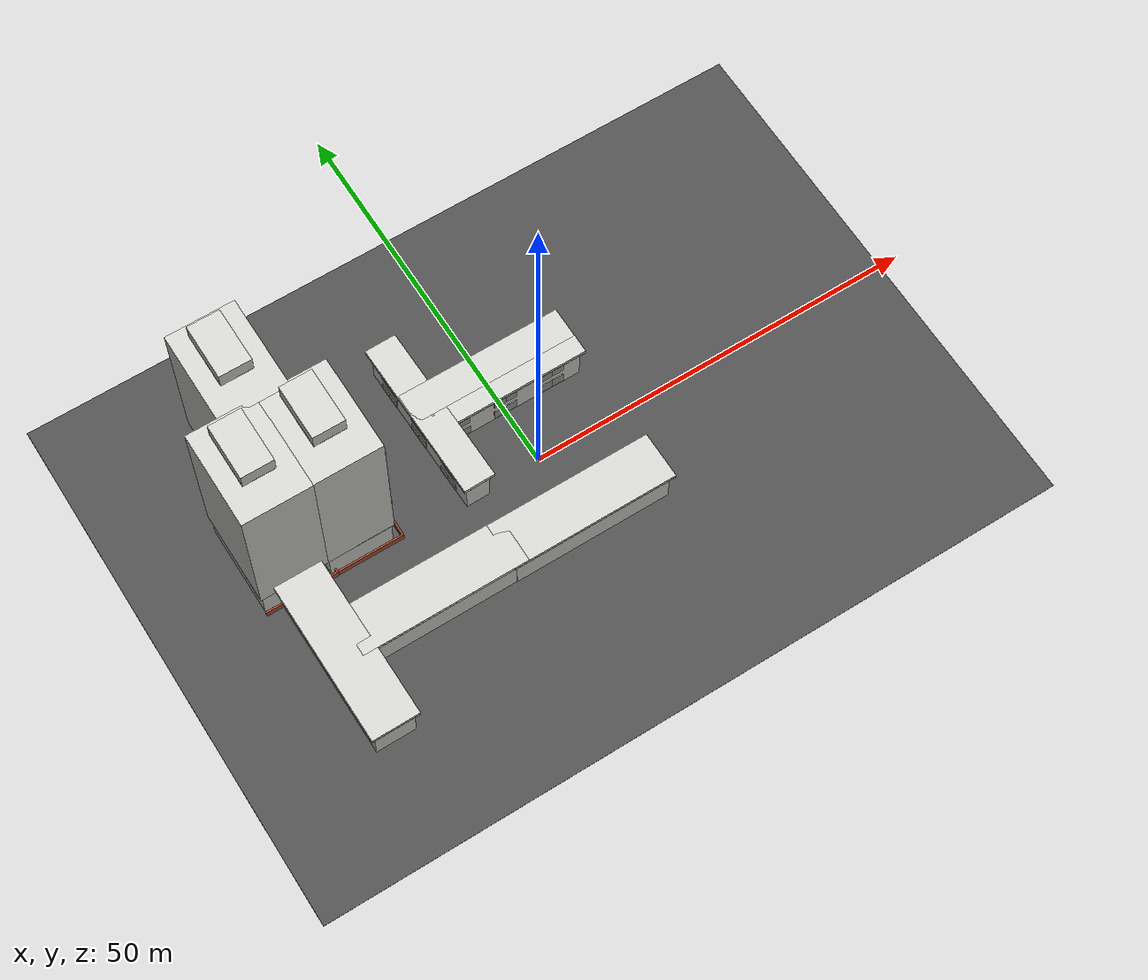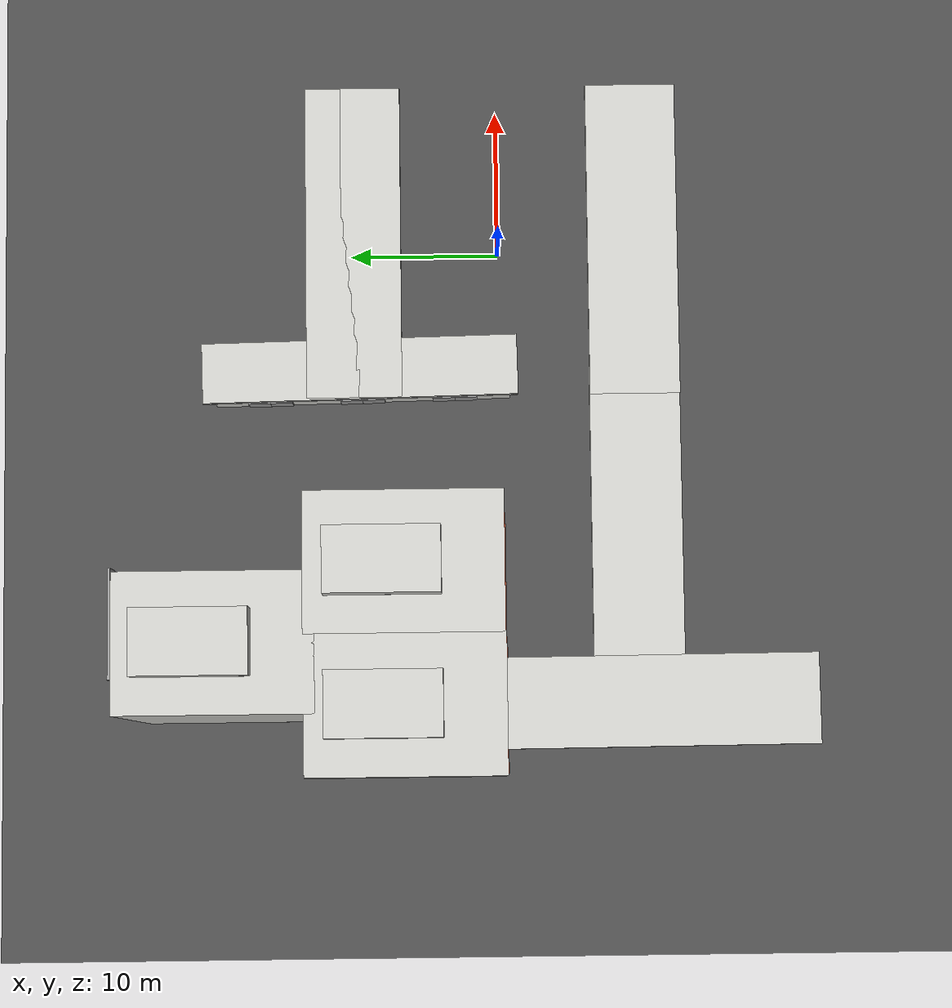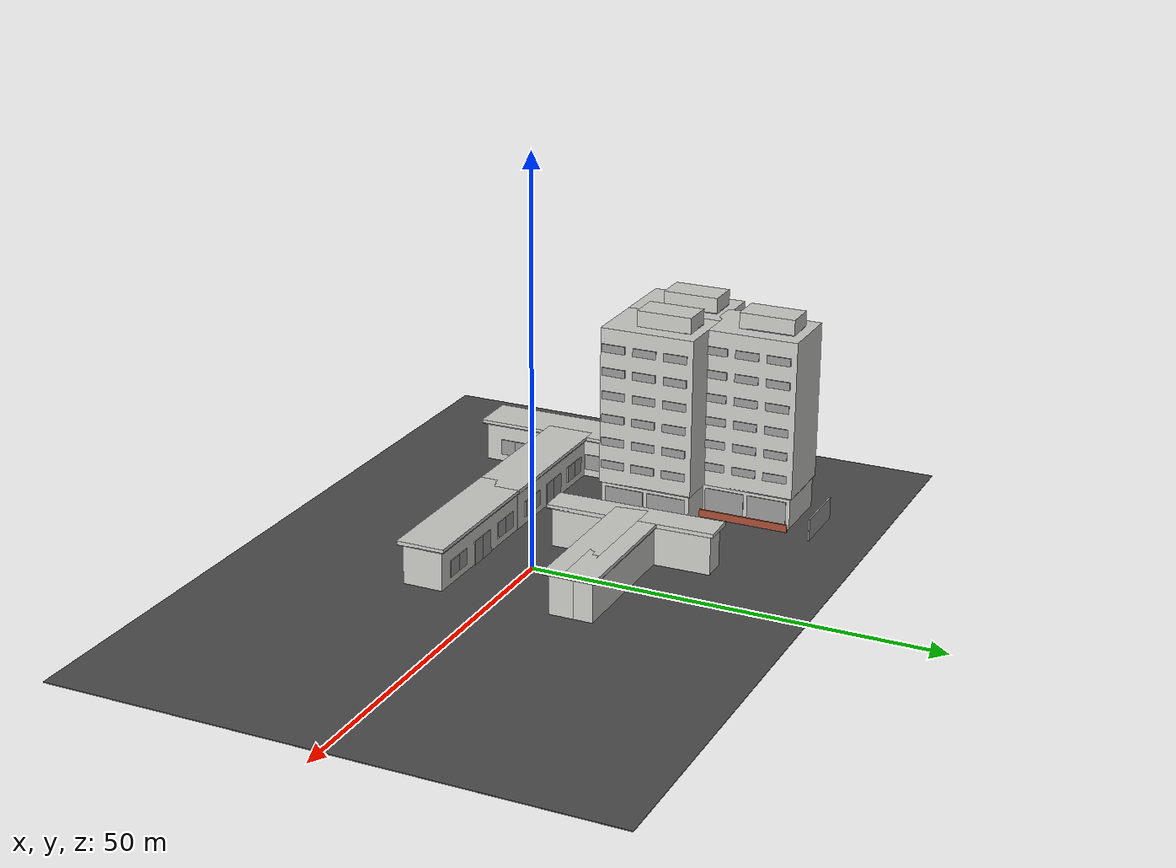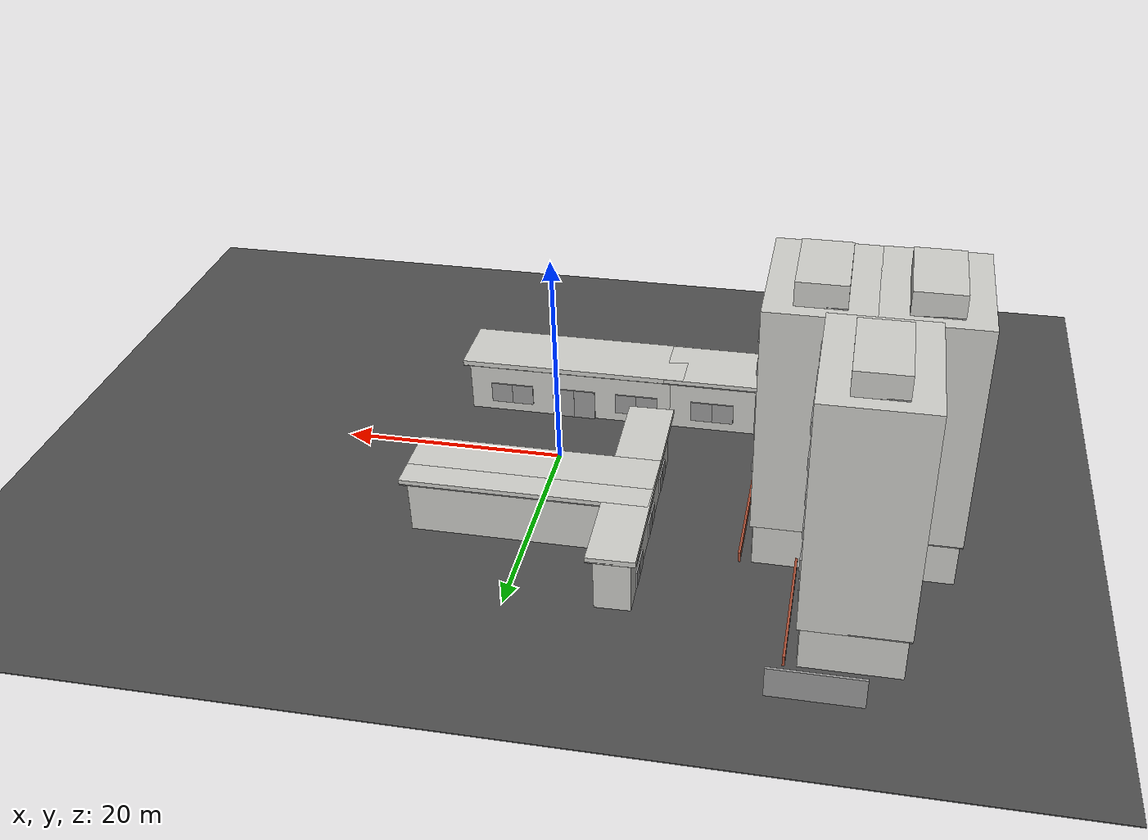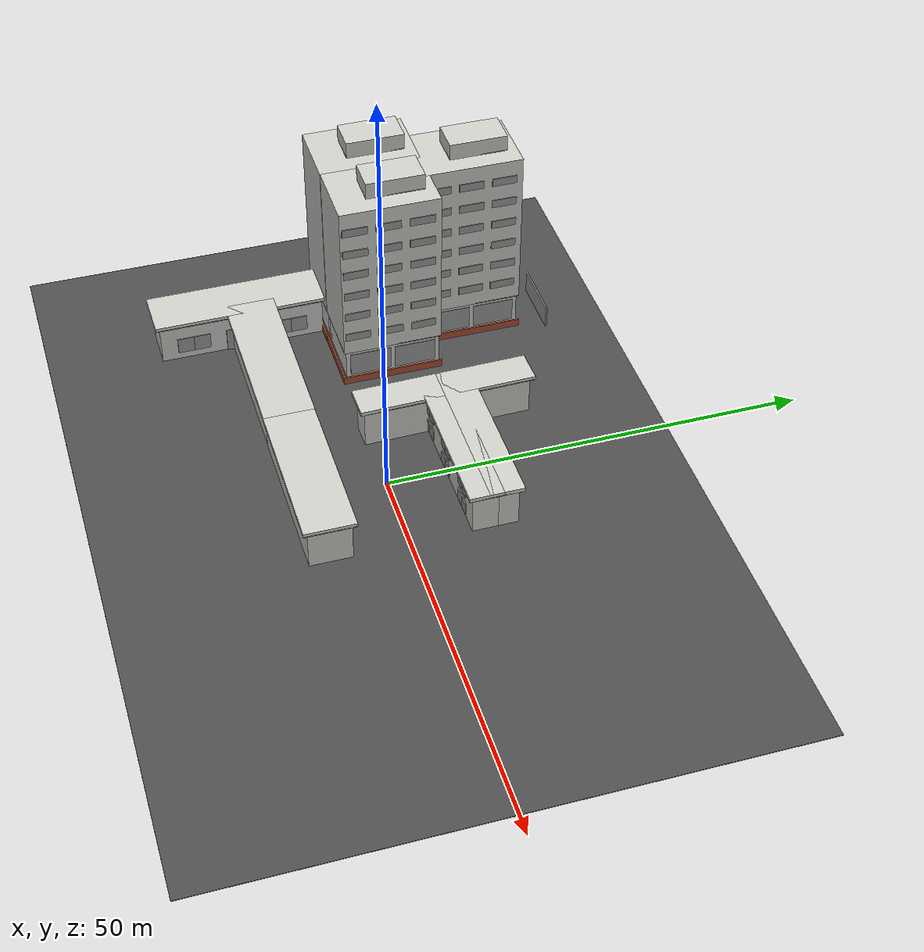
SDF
<sdf version="1.6">
 <world name="default">
  <light name="sun" type="directional">
   <pose>0 0 10 0 -0 0</pose>
   <diffuse>0.8 0.8 0.8 1</diffuse>
   <specular>0.2 0.2 0.2 1</specular>
   <attenuation>
    <range>1000</range>
    <constant>0.9</constant>
    <linear>0.01</linear>
    <quadratic>0.001</quadratic>
   </attenuation>
   <direction>-0.5 0.1 -0.9</direction>
  </light>
  <model name="asphalt_plane">
   <pose>-0.025745 0.03662 0 0 -0 0</pose>
   <static>1</static>
   <link name="link">
    <collision name="collision"><geometry><box><size>95.2534 67.6256 0.1</size></box></geometry></collision>
    <visual name="visual">
     <cast_shadows>0</cast_shadows>
     <geometry><box><size>95.2534 67.6256 0.1</size></box></geometry>
     <material>
      <script>
       <uri>model://asphalt_plane/materials/scripts</uri>
       <uri>model://asphalt_plane/materials/textures</uri>
       <name>vrc/asphalt</name>
      </script>
     </material>
    </visual>
   </link>
  </model>
  <model name="j_building">
   <pose>0.044289 -9.00814 0 0 -0 0</pose>
   <link name="Door_2">
    <collision name="Door_2_Collision">
     <geometry><box><size>2 0.17 3</size></box></geometry>
     <pose>0 0 1.5 0 -0 0</pose>
    </collision>
    <visual name="Door_2_Visual">
     <pose>0 0 1.5 0 -0 0</pose>
     <geometry><box><size>2 0.17 3</size></box></geometry>
     <material>
      <script><uri>file://media/materials/scripts/gazebo.material</uri><name>Gazebo/Grey</name></script>
     </material>
    </visual>
    <pose>-1 2.55 0 0 -0 3.13771</pose>
   </link>
   <link name="Door_3">
    <collision name="Door_3_Collision">
     <geometry><box><size>2 0.17 3</size></box></geometry>
     <pose>0 0 1.5 0 -0 0</pose>
    </collision>
    <visual name="Door_3_Visual">
     <pose>0 0 1.5 0 -0 0</pose>
     <geometry><box><size>2 0.17 3</size></box></geometry>
     <material>
      <script><uri>file://media/materials/scripts/gazebo.material</uri><name>Gazebo/Grey</name></script>
     </material>
    </visual>
    <pose>1 2.55 0 0 -0 3.13969</pose>
   </link>
   <link name="Floor_1">
    <collision name="Floor_1_Collision">
     <geometry><box><size>21 6 0.1</size></box></geometry>
     <pose>0 0 0.05 0 -0 0</pose>
    </collision>
    <visual name="Floor_1_Visual">
     <pose>0 0 0.05 0 -0 0</pose>
     <geometry><box><size>21 6 0.1</size></box></geometry>
     <material>
      <script><uri>file://media/materials/scripts/gazebo.material</uri><name>Gazebo/Grey</name></script>
      <ambient>1 1 1 1</ambient>
     </material>
    </visual>
    <pose>0 0 5 0 -0 0</pose>
   </link>
   <link name="Wall_10">
    <collision name="Wall_10_Collision">
     <geometry><box><size>21 6 0.5</size></box></geometry>
     <pose>0 0 0.25 0 -0 0</pose>
    </collision>
    <visual name="Wall_10_Visual">
     <pose>0 0 0.25 0 -0 0</pose>
     <geometry><box><size>21 6 0.5</size></box></geometry>
     <material>
      <script><uri>file://media/materials/scripts/gazebo.material</uri><name>Gazebo/CeilingTiled</name></script>
      <ambient>0.435294 0.796078 0.67451 1</ambient>
     </material>
    </visual>
    <pose>0 0 5 0 -0 0</pose>
   </link>
   <link name="Wall_7">
    <collision name="Wall_7_Collision">
     <geometry><box><size>20 5 5</size></box></geometry>
     <pose>0 0 2.5 0 -0 0</pose>
    </collision>
    <visual name="Wall_7_Visual">
     <pose>0 0 2.5 0 -0 0</pose>
     <geometry><box><size>20 5 5</size></box></geometry>
     <material>
      <script><uri>file://media/materials/scripts/gazebo.material</uri><name>Gazebo/CeilingTiled</name></script>
      <ambient>1 1 1 1</ambient>
     </material>
    </visual>
   </link>
   <link name="Window_6">
    <collision name="Window_6_Collision">
     <geometry><box><size>2 0.17 2</size></box></geometry>
     <pose>0 0 1 0 -0 0</pose>
    </collision>
    <visual name="Window_6_Visual">
     <pose>0 0 1 0 -0 0</pose>
     <geometry><box><size>2 0.17 2</size></box></geometry>
     <material>
      <script><uri>file://media/materials/scripts/gazebo.material</uri><name>Gazebo/Grey</name></script>
     </material>
    </visual>
    <pose>-7 2.55 1 0 -0 3.13833</pose>
   </link>
   <link name="Window_7">
    <collision name="Window_7_Collision">
     <geometry><box><size>2 0.17 2</size></box></geometry>
     <pose>0 0 1 0 -0 0</pose>
    </collision>
    <visual name="Window_7_Visual">
     <pose>0 0 1 0 -0 0</pose>
     <geometry><box><size>2 0.17 2</size></box></geometry>
     <material>
      <script><uri>file://media/materials/scripts/gazebo.material</uri><name>Gazebo/Grey</name></script>
     </material>
    </visual>
    <pose>-5 2.55 1 0 -0 3.14106</pose>
   </link>
   <link name="Window_8">
    <collision name="Window_8_Collision">
     <geometry><box><size>2 0.17 2</size></box></geometry>
     <pose>0 0 1 0 -0 0</pose>
    </collision>
    <visual name="Window_8_Visual">
     <pose>0 0 1 0 -0 0</pose>
     <geometry><box><size>2 0.17 2</size></box></geometry>
     <material>
      <script><uri>file://media/materials/scripts/gazebo.material</uri><name>Gazebo/Grey</name></script>
     </material>
    </visual>
    <pose>5 2.55 1 0 0 -3.13877</pose>
   </link>
   <link name="Window_9">
    <collision name="Window_9_Collision">
     <geometry><box><size>2 0.17 2</size></box></geometry>
     <pose>0 0 1 0 -0 0</pose>
    </collision>
    <visual name="Window_9_Visual">
     <pose>0 0 1 0 -0 0</pose>
     <geometry><box><size>2 0.17 2</size></box></geometry>
     <material>
      <script><uri>file://media/materials/scripts/gazebo.material</uri><name>Gazebo/Grey</name></script>
     </material>
    </visual>
    <pose>7 2.55 1 0 0 -3.13955</pose>
   </link>
   <static>1</static>
  </model>
  <model name="k_building">
   <pose>0 8.5 0 0 -0 0</pose>
   <link name="Floor_0">
    <collision name="Floor_0_Collision">
     <geometry><box><size>21 4 0.1</size></box></geometry>
     <pose>0 0 0.05 0 -0 0</pose>
    </collision>
    <visual name="Floor_0_Visual">
     <pose>0 0 0.05 0 -0 0</pose>
     <geometry><box><size>21 4 0.1</size></box></geometry>
     <material>
      <script><uri>file://media/materials/scripts/gazebo.material</uri><name>Gazebo/Grey</name></script>
      <ambient>1 1 1 1</ambient>
     </material>
    </visual>
    <pose>0 0 5 0 -0 0</pose>
   </link>
   <link name="Wall_0">
    <collision name="Wall_0_Collision">
     <geometry><box><size>20 3 5</size></box></geometry>
     <pose>0 0 2.5 0 -0 0</pose>
    </collision>
    <visual name="Wall_0_Visual">
     <pose>0 0 2.5 0 -0 0</pose>
     <geometry><box><size>20 3 5</size></box></geometry>
     <material>
      <script><uri>file://media/materials/scripts/gazebo.material</uri><name>Gazebo/CeilingTiled</name></script>
      <ambient>1 1 1 1</ambient>
     </material>
    </visual>
   </link>
   <link name="Wall_3">
    <collision name="Wall_3_Collision">
     <geometry><box><size>21 4 0.5</size></box></geometry>
     <pose>0 0 0.25 0 -0 0</pose>
    </collision>
    <visual name="Wall_3_Visual">
     <pose>0 0 0.25 0 -0 0</pose>
     <geometry><box><size>21 4 0.5</size></box></geometry>
     <material>
      <script><uri>file://media/materials/scripts/gazebo.material</uri><name>Gazebo/CeilingTiled</name></script>
      <ambient>0.435294 0.796078 0.67451 1</ambient>
     </material>
    </visual>
    <pose>0 0 5 0 -0 0</pose>
   </link>
   <link name="Window_0">
    <collision name="Window_0_Collision">
     <geometry><box><size>1.5 0.17 1.5</size></box></geometry>
     <pose>0 0 0.75 0 -0 0</pose>
    </collision>
    <visual name="Window_0_Visual">
     <pose>0 0 0.75 0 -0 0</pose>
     <geometry><box><size>1.5 0.17 1.5</size></box></geometry>
     <material>
      <script><uri>file://media/materials/scripts/gazebo.material</uri><name>Gazebo/Grey</name></script>
     </material>
    </visual>
    <pose>-7 -1.55 0.5 0 -0 0</pose>
   </link>
   <link name="Window_1">
    <collision name="Window_1_Collision">
     <geometry><box><size>1.5 0.17 1.5</size></box></geometry>
     <pose>0 0 0.75 0 -0 0</pose>
    </collision>
    <visual name="Window_1_Visual">
     <pose>0 0 0.75 0 -0 0</pose>
     <geometry><box><size>1.5 0.17 1.5</size></box></geometry>
     <material>
      <script><uri>file://media/materials/scripts/gazebo.material</uri><name>Gazebo/Grey</name></script>
     </material>
    </visual>
    <pose>-5.5 -1.55 0.5 0 -0 0</pose>
   </link>
   <link name="Window_10">
    <collision name="Window_10_Collision">
     <geometry><box><size>1.5 0.17 1.5</size></box></geometry>
     <pose>0 0 0.75 0 -0 0</pose>
    </collision>
    <visual name="Window_10_Visual">
     <pose>0 0 0.75 0 -0 0</pose>
     <geometry><box><size>1.5 0.17 1.5</size></box></geometry>
     <material>
      <script><uri>file://media/materials/scripts/gazebo.material</uri><name>Gazebo/Grey</name></script>
     </material>
    </visual>
    <pose>5.5 -1.55 3 0 -0 0</pose>
   </link>
   <link name="Window_11">
    <collision name="Window_11_Collision">
     <geometry><box><size>1.5 0.17 1.5</size></box></geometry>
     <pose>0 0 0.75 0 -0 0</pose>
    </collision>
    <visual name="Window_11_Visual">
     <pose>0 0 0.75 0 -0 0</pose>
     <geometry><box><size>1.5 0.17 1.5</size></box></geometry>
     <material>
      <script><uri>file://media/materials/scripts/gazebo.material</uri><name>Gazebo/Grey</name></script>
     </material>
    </visual>
    <pose>7 -1.55 3 0 -0 0</pose>
   </link>
   <link name="Window_2">
    <collision name="Window_2_Collision">
     <geometry><box><size>1.5 0.17 1.5</size></box></geometry>
     <pose>0 0 0.75 0 -0 0</pose>
    </collision>
    <visual name="Window_2_Visual">
     <pose>0 0 0.75 0 -0 0</pose>
     <geometry><box><size>1.5 0.17 1.5</size></box></geometry>
     <material>
      <script><uri>file://media/materials/scripts/gazebo.material</uri><name>Gazebo/Grey</name></script>
     </material>
    </visual>
    <pose>-0.75 -1.55 0.5 0 -0 0</pose>
   </link>
   <link name="Window_3">
    <collision name="Window_3_Collision">
     <geometry><box><size>1.5 0.17 1.5</size></box></geometry>
     <pose>0 0 0.75 0 -0 0</pose>
    </collision>
    <visual name="Window_3_Visual">
     <pose>0 0 0.75 0 -0 0</pose>
     <geometry><box><size>1.5 0.17 1.5</size></box></geometry>
     <material>
      <script><uri>file://media/materials/scripts/gazebo.material</uri><name>Gazebo/Grey</name></script>
     </material>
    </visual>
    <pose>0.75 -1.55 0.5 0 -0 0</pose>
   </link>
   <link name="Window_4">
    <collision name="Window_4_Collision">
     <geometry><box><size>1.5 0.17 1.5</size></box></geometry>
     <pose>0 0 0.75 0 -0 0</pose>
    </collision>
    <visual name="Window_4_Visual">
     <pose>0 0 0.75 0 -0 0</pose>
     <geometry><box><size>1.5 0.17 1.5</size></box></geometry>
     <material>
      <script><uri>file://media/materials/scripts/gazebo.material</uri><name>Gazebo/Grey</name></script>
     </material>
    </visual>
    <pose>5.5 -1.55 0.5 0 -0 0</pose>
   </link>
   <link name="Window_5">
    <collision name="Window_5_Collision">
     <geometry><box><size>1.5 0.17 1.5</size></box></geometry>
     <pose>0 0 0.75 0 -0 0</pose>
    </collision>
    <visual name="Window_5_Visual">
     <pose>0 0 0.75 0 -0 0</pose>
     <geometry><box><size>1.5 0.17 1.5</size></box></geometry>
     <material>
      <script><uri>file://media/materials/scripts/gazebo.material</uri><name>Gazebo/Grey</name></script>
     </material>
    </visual>
    <pose>7 -1.55 0.5 0 -0 0</pose>
   </link>
   <link name="Window_6">
    <collision name="Window_6_Collision">
     <geometry><box><size>1.5 0.17 1.5</size></box></geometry>
     <pose>0 0 0.75 0 -0 0</pose>
    </collision>
    <visual name="Window_6_Visual">
     <pose>0 0 0.75 0 -0 0</pose>
     <geometry><box><size>1.5 0.17 1.5</size></box></geometry>
     <material>
      <script><uri>file://media/materials/scripts/gazebo.material</uri><name>Gazebo/Grey</name></script>
     </material>
    </visual>
    <pose>-7 -1.55 3 0 -0 0</pose>
   </link>
   <link name="Window_7">
    <collision name="Window_7_Collision">
     <geometry><box><size>1.5 0.17 1.5</size></box></geometry>
     <pose>0 0 0.75 0 -0 0</pose>
    </collision>
    <visual name="Window_7_Visual">
     <pose>0 0 0.75 0 -0 0</pose>
     <geometry><box><size>1.5 0.17 1.5</size></box></geometry>
     <material>
      <script><uri>file://media/materials/scripts/gazebo.material</uri><name>Gazebo/Grey</name></script>
     </material>
    </visual>
    <pose>-5.5 -1.55 3 0 -0 0</pose>
   </link>
   <link name="Window_8">
    <collision name="Window_8_Collision">
     <geometry><box><size>1.5 0.17 1.5</size></box></geometry>
     <pose>0 0 0.75 0 -0 0</pose>
    </collision>
    <visual name="Window_8_Visual">
     <pose>0 0 0.75 0 -0 0</pose>
     <geometry><box><size>1.5 0.17 1.5</size></box></geometry>
     <material>
      <script><uri>file://media/materials/scripts/gazebo.material</uri><name>Gazebo/Grey</name></script>
     </material>
    </visual>
    <pose>-0.75 -1.55 3 0 -0 0</pose>
   </link>
   <link name="Window_9">
    <collision name="Window_9_Collision">
     <geometry><box><size>1.5 0.17 1.5</size></box></geometry>
     <pose>0 0 0.75 0 -0 0</pose>
    </collision>
    <visual name="Window_9_Visual">
     <pose>0 0 0.75 0 -0 0</pose>
     <geometry><box><size>1.5 0.17 1.5</size></box></geometry>
     <material>
      <script><uri>file://media/materials/scripts/gazebo.material</uri><name>Gazebo/Grey</name></script>
     </material>
    </visual>
    <pose>0.75 -1.55 3 0 -0 0</pose>
   </link>
   <static>1</static>
  </model>
  <model name="info_building">
   <pose>-22.5368 5.87118 0 0 -0 0</pose>
   <link name="Door_1">
    <collision name="Door_1_Collision">
     <geometry><box><size>5 0.17 3</size></box></geometry>
     <pose>0 0 1.5 0 -0 0</pose>
    </collision>
    <visual name="Door_1_Visual">
     <pose>0 0 1.5 0 -0 0</pose>
     <geometry><box><size>5 0.17 3</size></box></geometry>
     <material>
      <script><uri>file://media/materials/scripts/gazebo.material</uri><name>Gazebo/Grey</name></script>
     </material>
    </visual>
    <pose>3.575 -2.575 0.5 0 -0 1.56828</pose>
   </link>
   <link name="Door_2">
    <collision name="Door_2_Collision">
     <geometry><box><size>5 0.17 3</size></box></geometry>
     <pose>0 0 1.5 0 -0 0</pose>
    </collision>
    <visual name="Door_2_Visual">
     <pose>0 0 1.5 0 -0 0</pose>
     <geometry><box><size>5 0.17 3</size></box></geometry>
     <material>
      <script><uri>file://media/materials/scripts/gazebo.material</uri><name>Gazebo/Grey</name></script>
     </material>
    </visual>
    <pose>3.575 2.925 0.5 0 -0 1.5733</pose>
   </link>
   <link name="Floor_1">
    <collision name="Floor_1_Collision">
     <geometry><box><size>8.5 12 0.1</size></box></geometry>
     <pose>0 0 0.05 0 -0 0</pose>
    </collision>
    <visual name="Floor_1_Visual">
     <pose>0 0 0.05 0 -0 0</pose>
     <geometry><box><size>8.5 12 0.1</size></box></geometry>
     <material>
      <script><uri>file://media/materials/scripts/gazebo.material</uri><name>Gazebo/Grey</name></script>
      <ambient>1 1 1 1</ambient>
     </material>
    </visual>
    <pose>-0.425 0.174999 4 0 -0 0</pose>
   </link>
   <link name="Floor_2">
    <collision name="Floor_2_Collision">
     <geometry><box><size>4 7 0.1</size></box></geometry>
     <pose>0 0 0.05 0 -0 0</pose>
    </collision>
    <visual name="Floor_2_Visual">
     <pose>0 0 0.05 0 -0 0</pose>
     <geometry><box><size>4 7 0.1</size></box></geometry>
     <material>
      <script><uri>file://media/materials/scripts/gazebo.material</uri><name>Gazebo/Grey</name></script>
      <ambient>1 1 1 1</ambient>
     </material>
    </visual>
    <pose>-0.425 1.425 24 0 -0 0</pose>
   </link>
   <link name="Wall_11">
    <collision name="Wall_11_Collision">
     <geometry><box><size>12.2 0.2 1</size></box></geometry>
     <pose>0 0 0.5 0 -0 0</pose>
    </collision>
    <visual name="Wall_11_Visual">
     <pose>0 0 0.5 0 -0 0</pose>
     <geometry><box><size>12.2 0.2 1</size></box></geometry>
     <material>
      <script><uri>file://media/materials/scripts/gazebo.material</uri><name>Gazebo/Bricks</name></script>
      <ambient>1 1 1 1</ambient>
     </material>
    </visual>
    <pose>4.575 -0.075001 0 0 -0 1.5708</pose>
   </link>
   <link name="Wall_15">
    <collision name="Wall_15_Collision">
     <geometry><box><size>11.5 8 4</size></box></geometry>
     <pose>0 0 2 0 -0 0</pose>
    </collision>
    <visual name="Wall_15_Visual">
     <pose>0 0 2 0 -0 0</pose>
     <geometry><box><size>11.5 8 4</size></box></geometry>
     <material>
      <script><uri>file://media/materials/scripts/gazebo.material</uri><name>Gazebo/CeilingTiled</name></script>
      <ambient>0.231373 0.141176 0.0509804 1</ambient>
     </material>
    </visual>
    <pose>-0.425 0.174999 0 0 -0 1.5708</pose>
   </link>
   <link name="Wall_19">
    <collision name="Wall_19_Collision">
     <geometry><box><size>12 8.5 20</size></box></geometry>
     <pose>0 0 10 0 -0 0</pose>
    </collision>
    <visual name="Wall_19_Visual">
     <pose>0 0 10 0 -0 0</pose>
     <geometry><box><size>12 8.5 20</size></box></geometry>
     <material>
      <script><uri>file://media/materials/scripts/gazebo.material</uri><name>Gazebo/CeilingTiled</name></script>
      <ambient>0.505882 0.505882 0.505882 1</ambient>
     </material>
    </visual>
    <pose>-0.425 0.174999 4 0 -0 1.5708</pose>
   </link>
   <link name="Wall_20">
    <collision name="Wall_20_Collision">
     <geometry><box><size>7 4 2</size></box></geometry>
     <pose>0 0 1 0 -0 0</pose>
    </collision>
    <visual name="Wall_20_Visual">
     <pose>0 0 1 0 -0 0</pose>
     <geometry><box><size>7 4 2</size></box></geometry>
     <material>
      <script><uri>file://media/materials/scripts/gazebo.material</uri><name>Gazebo/CeilingTiled</name></script>
      <ambient>0.435294 0.796078 0.67451 1</ambient>
     </material>
    </visual>
    <pose>-0.425 1.425 24 0 -0 1.5708</pose>
   </link>
   <link name="Wall_9">
    <collision name="Wall_9_Collision">
     <geometry><box><size>9.2 0.2 1</size></box></geometry>
     <pose>0 0 0.5 0 -0 0</pose>
    </collision>
    <visual name="Wall_9_Visual">
     <pose>0 0 0.5 0 -0 0</pose>
     <geometry><box><size>9.2 0.2 1</size></box></geometry>
     <material>
      <script><uri>file://media/materials/scripts/gazebo.material</uri><name>Gazebo/Bricks</name></script>
      <ambient>1 1 1 1</ambient>
     </material>
    </visual>
    <pose>0.075 -6.075 0 0 -0 3.14159</pose>
   </link>
   <link name="Window_0">
    <collision name="Window_0_Collision">
     <geometry><box><size>3 0.17 1</size></box></geometry>
     <pose>0 0 0.5 0 -0 0</pose>
    </collision>
    <visual name="Window_0_Visual">
     <pose>0 0 0.5 0 -0 0</pose>
     <geometry><box><size>3 0.17 1</size></box></geometry>
     <material>
      <script><uri>file://media/materials/scripts/gazebo.material</uri><name>Gazebo/Grey</name></script>
     </material>
    </visual>
    <pose>3.875 -4.075 6 0 -0 1.57704</pose>
   </link>
   <link name="Window_11">
    <collision name="Window_11_Collision">
     <geometry><box><size>3 0.17 1</size></box></geometry>
     <pose>0 0 0.5 0 -0 0</pose>
    </collision>
    <visual name="Window_11_Visual">
     <pose>0 0 0.5 0 -0 0</pose>
     <geometry><box><size>3 0.17 1</size></box></geometry>
     <material>
      <script><uri>file://media/materials/scripts/gazebo.material</uri><name>Gazebo/Grey</name></script>
     </material>
    </visual>
    <pose>3.875 -4.075 15 0 -0 1.57983</pose>
   </link>
   <link name="Window_12">
    <collision name="Window_12_Collision">
     <geometry><box><size>3 0.17 1</size></box></geometry>
     <pose>0 0 0.5 0 -0 0</pose>
    </collision>
    <visual name="Window_12_Visual">
     <pose>0 0 0.5 0 -0 0</pose>
     <geometry><box><size>3 0.17 1</size></box></geometry>
     <material>
      <script><uri>file://media/materials/scripts/gazebo.material</uri><name>Gazebo/Grey</name></script>
     </material>
    </visual>
    <pose>3.875 -0.075001 15 0 -0 1.58105</pose>
   </link>
   <link name="Window_13">
    <collision name="Window_13_Collision">
     <geometry><box><size>3 0.17 1</size></box></geometry>
     <pose>0 0 0.5 0 -0 0</pose>
    </collision>
    <visual name="Window_13_Visual">
     <pose>0 0 0.5 0 -0 0</pose>
     <geometry><box><size>3 0.17 1</size></box></geometry>
     <material>
      <script><uri>file://media/materials/scripts/gazebo.material</uri><name>Gazebo/Grey</name></script>
     </material>
    </visual>
    <pose>3.875 3.925 15 0 -0 1.57717</pose>
   </link>
   <link name="Window_14">
    <collision name="Window_14_Collision">
     <geometry><box><size>3 0.17 1</size></box></geometry>
     <pose>0 0 0.5 0 -0 0</pose>
    </collision>
    <visual name="Window_14_Visual">
     <pose>0 0 0.5 0 -0 0</pose>
     <geometry><box><size>3 0.17 1</size></box></geometry>
     <material>
      <script><uri>file://media/materials/scripts/gazebo.material</uri><name>Gazebo/Grey</name></script>
     </material>
    </visual>
    <pose>3.875 -4.075 18 0 -0 1.55591</pose>
   </link>
   <link name="Window_15">
    <collision name="Window_15_Collision">
     <geometry><box><size>3 0.17 1</size></box></geometry>
     <pose>0 0 0.5 0 -0 0</pose>
    </collision>
    <visual name="Window_15_Visual">
     <pose>0 0 0.5 0 -0 0</pose>
     <geometry><box><size>3 0.17 1</size></box></geometry>
     <material>
      <script><uri>file://media/materials/scripts/gazebo.material</uri><name>Gazebo/Grey</name></script>
     </material>
    </visual>
    <pose>3.875 -0.075001 18 0 -0 1.57217</pose>
   </link>
   <link name="Window_16">
    <collision name="Window_16_Collision">
     <geometry><box><size>3 0.17 1</size></box></geometry>
     <pose>0 0 0.5 0 -0 0</pose>
    </collision>
    <visual name="Window_16_Visual">
     <pose>0 0 0.5 0 -0 0</pose>
     <geometry><box><size>3 0.17 1</size></box></geometry>
     <material>
      <script><uri>file://media/materials/scripts/gazebo.material</uri><name>Gazebo/Grey</name></script>
     </material>
    </visual>
    <pose>3.875 3.925 18 0 -0 1.56411</pose>
   </link>
   <link name="Window_17">
    <collision name="Window_17_Collision">
     <geometry><box><size>3 0.17 1</size></box></geometry>
     <pose>0 0 0.5 0 -0 0</pose>
    </collision>
    <visual name="Window_17_Visual">
     <pose>0 0 0.5 0 -0 0</pose>
     <geometry><box><size>3 0.17 1</size></box></geometry>
     <material>
      <script><uri>file://media/materials/scripts/gazebo.material</uri><name>Gazebo/Grey</name></script>
     </material>
    </visual>
    <pose>3.875 -4.075 21 0 -0 1.57699</pose>
   </link>
   <link name="Window_18">
    <collision name="Window_18_Collision">
     <geometry><box><size>3 0.17 1</size></box></geometry>
     <pose>0 0 0.5 0 -0 0</pose>
    </collision>
    <visual name="Window_18_Visual">
     <pose>0 0 0.5 0 -0 0</pose>
     <geometry><box><size>3 0.17 1</size></box></geometry>
     <material>
      <script><uri>file://media/materials/scripts/gazebo.material</uri><name>Gazebo/Grey</name></script>
     </material>
    </visual>
    <pose>3.875 -0.075001 21 0 -0 1.57095</pose>
   </link>
   <link name="Window_19">
    <collision name="Window_19_Collision">
     <geometry><box><size>3 0.17 1</size></box></geometry>
     <pose>0 0 0.5 0 -0 0</pose>
    </collision>
    <visual name="Window_19_Visual">
     <pose>0 0 0.5 0 -0 0</pose>
     <geometry><box><size>3 0.17 1</size></box></geometry>
     <material>
      <script><uri>file://media/materials/scripts/gazebo.material</uri><name>Gazebo/Grey</name></script>
     </material>
    </visual>
    <pose>3.875 3.925 21 0 -0 1.5708</pose>
   </link>
   <link name="Window_2">
    <collision name="Window_2_Collision">
     <geometry><box><size>3 0.17 1</size></box></geometry>
     <pose>0 0 0.5 0 -0 0</pose>
    </collision>
    <visual name="Window_2_Visual">
     <pose>0 0 0.5 0 -0 0</pose>
     <geometry><box><size>3 0.17 1</size></box></geometry>
     <material>
      <script><uri>file://media/materials/scripts/gazebo.material</uri><name>Gazebo/Grey</name></script>
     </material>
    </visual>
    <pose>3.875 -0.075001 6 0 -0 1.5855</pose>
   </link>
   <link name="Window_3">
    <collision name="Window_3_Collision">
     <geometry><box><size>3 0.17 1</size></box></geometry>
     <pose>0 0 0.5 0 -0 0</pose>
    </collision>
    <visual name="Window_3_Visual">
     <pose>0 0 0.5 0 -0 0</pose>
     <geometry><box><size>3 0.17 1</size></box></geometry>
     <material>
      <script><uri>file://media/materials/scripts/gazebo.material</uri><name>Gazebo/Grey</name></script>
     </material>
    </visual>
    <pose>3.875 3.925 6 0 -0 1.60806</pose>
   </link>
   <link name="Window_4">
    <collision name="Window_4_Collision">
     <geometry><box><size>3 0.17 1</size></box></geometry>
     <pose>0 0 0.5 0 -0 0</pose>
    </collision>
    <visual name="Window_4_Visual">
     <pose>0 0 0.5 0 -0 0</pose>
     <geometry><box><size>3 0.17 1</size></box></geometry>
     <material>
      <script><uri>file://media/materials/scripts/gazebo.material</uri><name>Gazebo/Grey</name></script>
     </material>
    </visual>
    <pose>3.875 -0.075001 9 0 -0 1.58223</pose>
   </link>
   <link name="Window_5">
    <collision name="Window_5_Collision">
     <geometry><box><size>3 0.17 1</size></box></geometry>
     <pose>0 0 0.5 0 -0 0</pose>
    </collision>
    <visual name="Window_5_Visual">
     <pose>0 0 0.5 0 -0 0</pose>
     <geometry><box><size>3 0.17 1</size></box></geometry>
     <material>
      <script><uri>file://media/materials/scripts/gazebo.material</uri><name>Gazebo/Grey</name></script>
     </material>
    </visual>
    <pose>3.875 -4.075 9 0 -0 1.60111</pose>
   </link>
   <link name="Window_6">
    <collision name="Window_6_Collision">
     <geometry><box><size>3 0.17 1</size></box></geometry>
     <pose>0 0 0.5 0 -0 0</pose>
    </collision>
    <visual name="Window_6_Visual">
     <pose>0 0 0.5 0 -0 0</pose>
     <geometry><box><size>3 0.17 1</size></box></geometry>
     <material>
      <script><uri>file://media/materials/scripts/gazebo.material</uri><name>Gazebo/Grey</name></script>
     </material>
    </visual>
    <pose>3.875 3.925 9 0 -0 1.55202</pose>
   </link>
   <link name="Window_7">
    <collision name="Window_7_Collision">
     <geometry><box><size>3 0.17 1</size></box></geometry>
     <pose>0 0 0.5 0 -0 0</pose>
    </collision>
    <visual name="Window_7_Visual">
     <pose>0 0 0.5 0 -0 0</pose>
     <geometry><box><size>3 0.17 1</size></box></geometry>
     <material>
      <script><uri>file://media/materials/scripts/gazebo.material</uri><name>Gazebo/Grey</name></script>
     </material>
    </visual>
    <pose>3.875 -4.075 12 0 -0 1.5708</pose>
   </link>
   <link name="Window_8">
    <collision name="Window_8_Collision">
     <geometry><box><size>3 0.17 1</size></box></geometry>
     <pose>0 0 0.5 0 -0 0</pose>
    </collision>
    <visual name="Window_8_Visual">
     <pose>0 0 0.5 0 -0 0</pose>
     <geometry><box><size>3 0.17 1</size></box></geometry>
     <material>
      <script><uri>file://media/materials/scripts/gazebo.material</uri><name>Gazebo/Grey</name></script>
     </material>
    </visual>
    <pose>3.875 -0.075001 12 0 -0 1.56933</pose>
   </link>
   <link name="Window_9">
    <collision name="Window_9_Collision">
     <geometry><box><size>3 0.17 1</size></box></geometry>
     <pose>0 0 0.5 0 -0 0</pose>
    </collision>
    <visual name="Window_9_Visual">
     <pose>0 0 0.5 0 -0 0</pose>
     <geometry><box><size>3 0.17 1</size></box></geometry>
     <material>
      <script><uri>file://media/materials/scripts/gazebo.material</uri><name>Gazebo/Grey</name></script>
     </material>
    </visual>
    <pose>3.875 3.925 12 0 -0 1.57549</pose>
   </link>
   <static>1</static>
  </model>
  <physics name="default_physics" default="0" type="ode">
   <ode>
    <solver>
     <type>quick</type>
     <iters>10</iters>
     <sor>1.3</sor>
     <use_dynamic_moi_rescaling>0</use_dynamic_moi_rescaling>
    </solver>
    <constraints>
     <cfm>0</cfm>
     <erp>0.2</erp>
     <contact_max_correcting_vel>100</contact_max_correcting_vel>
     <contact_surface_layer>0.001</contact_surface_layer>
    </constraints>
   </ode>
   <max_step_size>0.002</max_step_size>
   <real_time_factor>1</real_time_factor>
   <real_time_update_rate>500</real_time_update_rate>
  </physics>
  <gravity>0 0 -9.8066</gravity>
  <magnetic_field>6e-06 2.3e-05 -4.2e-05</magnetic_field>
  <atmosphere type="adiabatic"/>
  <scene><ambient>0.4 0.4 0.4 1</ambient><background>0.7 0.7 0.7 1</background><shadows>1</shadows></scene>
  <spherical_coordinates>
   <surface_model>EARTH_WGS84</surface_model>
   <latitude_deg>0</latitude_deg>
   <longitude_deg>0</longitude_deg>
   <elevation>0</elevation>
   <heading_deg>0</heading_deg>
  </spherical_coordinates>
  <model name="k_building_clone">
   <pose>-0.013988 10.8554 0 0 -0 0</pose>
   <link name="Floor_0">
    <collision name="Floor_0_Collision">
     <geometry><box><size>21 4 0.1</size></box></geometry>
     <pose>0 0 0.05 0 -0 0</pose>
    </collision>
    <visual name="Floor_0_Visual">
     <pose>0 0 0.05 0 -0 0</pose>
     <geometry><box><size>21 4 0.1</size></box></geometry>
     <material>
      <script><uri>file://media/materials/scripts/gazebo.material</uri><name>Gazebo/Grey</name></script>
      <ambient>1 1 1 1</ambient>
     </material>
    </visual>
    <pose>0 0 5 0 -0 0</pose>
   </link>
   <link name="Wall_0">
    <collision name="Wall_0_Collision">
     <geometry><box><size>20 3 5</size></box></geometry>
     <pose>0 0 2.5 0 -0 0</pose>
    </collision>
    <visual name="Wall_0_Visual">
     <pose>0 0 2.5 0 -0 0</pose>
     <geometry><box><size>20 3 5</size></box></geometry>
     <material>
      <script><uri>file://media/materials/scripts/gazebo.material</uri><name>Gazebo/CeilingTiled</name></script>
      <ambient>1 1 1 1</ambient>
     </material>
    </visual>
   </link>
   <link name="Wall_3">
    <collision name="Wall_3_Collision">
     <geometry><box><size>21 4 0.5</size></box></geometry>
     <pose>0 0 0.25 0 -0 0</pose>
    </collision>
    <visual name="Wall_3_Visual">
     <pose>0 0 0.25 0 -0 0</pose>
     <geometry><box><size>21 4 0.5</size></box></geometry>
     <material>
      <script><uri>file://media/materials/scripts/gazebo.material</uri><name>Gazebo/CeilingTiled</name></script>
      <ambient>0.435294 0.796078 0.67451 1</ambient>
     </material>
    </visual>
    <pose>0 0 5 0 -0 0</pose>
   </link>
   <link name="Window_0">
    <collision name="Window_0_Collision">
     <geometry><box><size>1.5 0.17 1.5</size></box></geometry>
     <pose>0 0 0.75 0 -0 0</pose>
    </collision>
    <visual name="Window_0_Visual">
     <pose>0 0 0.75 0 -0 0</pose>
     <geometry><box><size>1.5 0.17 1.5</size></box></geometry>
     <material>
      <script><uri>file://media/materials/scripts/gazebo.material</uri><name>Gazebo/Grey</name></script>
     </material>
    </visual>
    <pose>-7 -1.55 0.5 0 -0 0</pose>
   </link>
   <link name="Window_1">
    <collision name="Window_1_Collision">
     <geometry><box><size>1.5 0.17 1.5</size></box></geometry>
     <pose>0 0 0.75 0 -0 0</pose>
    </collision>
    <visual name="Window_1_Visual">
     <pose>0 0 0.75 0 -0 0</pose>
     <geometry><box><size>1.5 0.17 1.5</size></box></geometry>
     <material>
      <script><uri>file://media/materials/scripts/gazebo.material</uri><name>Gazebo/Grey</name></script>
     </material>
    </visual>
    <pose>-5.5 -1.55 0.5 0 -0 0</pose>
   </link>
   <link name="Window_10">
    <collision name="Window_10_Collision">
     <geometry><box><size>1.5 0.17 1.5</size></box></geometry>
     <pose>0 0 0.75 0 -0 0</pose>
    </collision>
    <visual name="Window_10_Visual">
     <pose>0 0 0.75 0 -0 0</pose>
     <geometry><box><size>1.5 0.17 1.5</size></box></geometry>
     <material>
      <script><uri>file://media/materials/scripts/gazebo.material</uri><name>Gazebo/Grey</name></script>
     </material>
    </visual>
    <pose>5.5 -1.55 3 0 -0 0</pose>
   </link>
   <link name="Window_11">
    <collision name="Window_11_Collision">
     <geometry><box><size>1.5 0.17 1.5</size></box></geometry>
     <pose>0 0 0.75 0 -0 0</pose>
    </collision>
    <visual name="Window_11_Visual">
     <pose>0 0 0.75 0 -0 0</pose>
     <geometry><box><size>1.5 0.17 1.5</size></box></geometry>
     <material>
      <script><uri>file://media/materials/scripts/gazebo.material</uri><name>Gazebo/Grey</name></script>
     </material>
    </visual>
    <pose>7 -1.55 3 0 -0 0</pose>
   </link>
   <link name="Window_2">
    <collision name="Window_2_Collision">
     <geometry><box><size>1.5 0.17 1.5</size></box></geometry>
     <pose>0 0 0.75 0 -0 0</pose>
    </collision>
    <visual name="Window_2_Visual">
     <pose>0 0 0.75 0 -0 0</pose>
     <geometry><box><size>1.5 0.17 1.5</size></box></geometry>
     <material>
      <script><uri>file://media/materials/scripts/gazebo.material</uri><name>Gazebo/Grey</name></script>
     </material>
    </visual>
    <pose>-0.75 -1.55 0.5 0 -0 0</pose>
   </link>
   <link name="Window_3">
    <collision name="Window_3_Collision">
     <geometry><box><size>1.5 0.17 1.5</size></box></geometry>
     <pose>0 0 0.75 0 -0 0</pose>
    </collision>
    <visual name="Window_3_Visual">
     <pose>0 0 0.75 0 -0 0</pose>
     <geometry><box><size>1.5 0.17 1.5</size></box></geometry>
     <material>
      <script><uri>file://media/materials/scripts/gazebo.material</uri><name>Gazebo/Grey</name></script>
     </material>
    </visual>
    <pose>0.75 -1.55 0.5 0 -0 0</pose>
   </link>
   <link name="Window_4">
    <collision name="Window_4_Collision">
     <geometry><box><size>1.5 0.17 1.5</size></box></geometry>
     <pose>0 0 0.75 0 -0 0</pose>
    </collision>
    <visual name="Window_4_Visual">
     <pose>0 0 0.75 0 -0 0</pose>
     <geometry><box><size>1.5 0.17 1.5</size></box></geometry>
     <material>
      <script><uri>file://media/materials/scripts/gazebo.material</uri><name>Gazebo/Grey</name></script>
     </material>
    </visual>
    <pose>5.5 -1.55 0.5 0 -0 0</pose>
   </link>
   <link name="Window_5">
    <collision name="Window_5_Collision">
     <geometry><box><size>1.5 0.17 1.5</size></box></geometry>
     <pose>0 0 0.75 0 -0 0</pose>
    </collision>
    <visual name="Window_5_Visual">
     <pose>0 0 0.75 0 -0 0</pose>
     <geometry><box><size>1.5 0.17 1.5</size></box></geometry>
     <material>
      <script><uri>file://media/materials/scripts/gazebo.material</uri><name>Gazebo/Grey</name></script>
     </material>
    </visual>
    <pose>7 -1.55 0.5 0 -0 0</pose>
   </link>
   <link name="Window_6">
    <collision name="Window_6_Collision">
     <geometry><box><size>1.5 0.17 1.5</size></box></geometry>
     <pose>0 0 0.75 0 -0 0</pose>
    </collision>
    <visual name="Window_6_Visual">
     <pose>0 0 0.75 0 -0 0</pose>
     <geometry><box><size>1.5 0.17 1.5</size></box></geometry>
     <material>
      <script><uri>file://media/materials/scripts/gazebo.material</uri><name>Gazebo/Grey</name></script>
     </material>
    </visual>
    <pose>-7 -1.55 3 0 -0 0</pose>
   </link>
   <link name="Window_7">
    <collision name="Window_7_Collision">
     <geometry><box><size>1.5 0.17 1.5</size></box></geometry>
     <pose>0 0 0.75 0 -0 0</pose>
    </collision>
    <visual name="Window_7_Visual">
     <pose>0 0 0.75 0 -0 0</pose>
     <geometry><box><size>1.5 0.17 1.5</size></box></geometry>
     <material>
      <script><uri>file://media/materials/scripts/gazebo.material</uri><name>Gazebo/Grey</name></script>
     </material>
    </visual>
    <pose>-5.5 -1.55 3 0 -0 0</pose>
   </link>
   <link name="Window_8">
    <collision name="Window_8_Collision">
     <geometry><box><size>1.5 0.17 1.5</size></box></geometry>
     <pose>0 0 0.75 0 -0 0</pose>
    </collision>
    <visual name="Window_8_Visual">
     <pose>0 0 0.75 0 -0 0</pose>
     <geometry><box><size>1.5 0.17 1.5</size></box></geometry>
     <material>
      <script><uri>file://media/materials/scripts/gazebo.material</uri><name>Gazebo/Grey</name></script>
     </material>
    </visual>
    <pose>-0.75 -1.55 3 0 -0 0</pose>
   </link>
   <link name="Window_9">
    <collision name="Window_9_Collision">
     <geometry><box><size>1.5 0.17 1.5</size></box></geometry>
     <pose>0 0 0.75 0 -0 0</pose>
    </collision>
    <visual name="Window_9_Visual">
     <pose>0 0 0.75 0 -0 0</pose>
     <geometry><box><size>1.5 0.17 1.5</size></box></geometry>
     <material>
      <script><uri>file://media/materials/scripts/gazebo.material</uri><name>Gazebo/Grey</name></script>
     </material>
    </visual>
    <pose>0.75 -1.55 3 0 -0 0</pose>
   </link>
   <static>1</static>
  </model>
  <model name="info_building_clone">
   <pose>-27.2285 17.1694 0 0 -0 0</pose>
   <link name="Door_1">
    <collision name="Door_1_Collision">
     <geometry><box><size>5 0.17 3</size></box></geometry>
     <pose>0 0 1.5 0 -0 0</pose>
    </collision>
    <visual name="Door_1_Visual">
     <pose>0 0 1.5 0 -0 0</pose>
     <geometry><box><size>5 0.17 3</size></box></geometry>
     <material>
      <script><uri>file://media/materials/scripts/gazebo.material</uri><name>Gazebo/Grey</name></script>
     </material>
    </visual>
    <pose>3.575 -2.575 0.5 0 -0 1.56828</pose>
   </link>
   <link name="Door_2">
    <collision name="Door_2_Collision">
     <geometry><box><size>5 0.17 3</size></box></geometry>
     <pose>0 0 1.5 0 -0 0</pose>
    </collision>
    <visual name="Door_2_Visual">
     <pose>0 0 1.5 0 -0 0</pose>
     <geometry><box><size>5 0.17 3</size></box></geometry>
     <material>
      <script><uri>file://media/materials/scripts/gazebo.material</uri><name>Gazebo/Grey</name></script>
     </material>
    </visual>
    <pose>3.575 2.925 0.5 0 -0 1.5733</pose>
   </link>
   <link name="Floor_1">
    <collision name="Floor_1_Collision">
     <geometry><box><size>8.5 12 0.1</size></box></geometry>
     <pose>0 0 0.05 0 -0 0</pose>
    </collision>
    <visual name="Floor_1_Visual">
     <pose>0 0 0.05 0 -0 0</pose>
     <geometry><box><size>8.5 12 0.1</size></box></geometry>
     <material>
      <script><uri>file://media/materials/scripts/gazebo.material</uri><name>Gazebo/Grey</name></script>
      <ambient>1 1 1 1</ambient>
     </material>
    </visual>
    <pose>-0.425 0.174999 4 0 -0 0</pose>
   </link>
   <link name="Floor_2">
    <collision name="Floor_2_Collision">
     <geometry><box><size>4 7 0.1</size></box></geometry>
     <pose>0 0 0.05 0 -0 0</pose>
    </collision>
    <visual name="Floor_2_Visual">
     <pose>0 0 0.05 0 -0 0</pose>
     <geometry><box><size>4 7 0.1</size></box></geometry>
     <material>
      <script><uri>file://media/materials/scripts/gazebo.material</uri><name>Gazebo/Grey</name></script>
      <ambient>1 1 1 1</ambient>
     </material>
    </visual>
    <pose>-0.425 1.425 24 0 -0 0</pose>
   </link>
   <link name="Wall_11">
    <collision name="Wall_11_Collision">
     <geometry><box><size>12.2 0.2 1</size></box></geometry>
     <pose>0 0 0.5 0 -0 0</pose>
    </collision>
    <visual name="Wall_11_Visual">
     <pose>0 0 0.5 0 -0 0</pose>
     <geometry><box><size>12.2 0.2 1</size></box></geometry>
     <material>
      <script><uri>file://media/materials/scripts/gazebo.material</uri><name>Gazebo/Bricks</name></script>
      <ambient>1 1 1 1</ambient>
     </material>
    </visual>
    <pose>4.575 -0.075001 0 0 -0 1.5708</pose>
   </link>
   <link name="Wall_15">
    <collision name="Wall_15_Collision">
     <geometry><box><size>11.5 8 4</size></box></geometry>
     <pose>0 0 2 0 -0 0</pose>
    </collision>
    <visual name="Wall_15_Visual">
     <pose>0 0 2 0 -0 0</pose>
     <geometry><box><size>11.5 8 4</size></box></geometry>
     <material>
      <script><uri>file://media/materials/scripts/gazebo.material</uri><name>Gazebo/CeilingTiled</name></script>
      <ambient>0.231373 0.141176 0.0509804 1</ambient>
     </material>
    </visual>
    <pose>-0.425 0.174999 0 0 -0 1.5708</pose>
   </link>
   <link name="Wall_19">
    <collision name="Wall_19_Collision">
     <geometry><box><size>12 8.5 20</size></box></geometry>
     <pose>0 0 10 0 -0 0</pose>
    </collision>
    <visual name="Wall_19_Visual">
     <pose>0 0 10 0 -0 0</pose>
     <geometry><box><size>12 8.5 20</size></box></geometry>
     <material>
      <script><uri>file://media/materials/scripts/gazebo.material</uri><name>Gazebo/CeilingTiled</name></script>
      <ambient>0.505882 0.505882 0.505882 1</ambient>
     </material>
    </visual>
    <pose>-0.425 0.174999 4 0 -0 1.5708</pose>
   </link>
   <link name="Wall_20">
    <collision name="Wall_20_Collision">
     <geometry><box><size>7 4 2</size></box></geometry>
     <pose>0 0 1 0 -0 0</pose>
    </collision>
    <visual name="Wall_20_Visual">
     <pose>0 0 1 0 -0 0</pose>
     <geometry><box><size>7 4 2</size></box></geometry>
     <material>
      <script><uri>file://media/materials/scripts/gazebo.material</uri><name>Gazebo/CeilingTiled</name></script>
      <ambient>0.435294 0.796078 0.67451 1</ambient>
     </material>
    </visual>
    <pose>-0.425 1.425 24 0 -0 1.5708</pose>
   </link>
   <link name="Wall_9">
    <collision name="Wall_9_Collision">
     <geometry><box><size>9.2 0.2 1</size></box></geometry>
     <pose>0 0 0.5 0 -0 0</pose>
    </collision>
    <visual name="Wall_9_Visual">
     <pose>0 0 0.5 0 -0 0</pose>
     <geometry><box><size>9.2 0.2 1</size></box></geometry>
     <material>
      <script><uri>file://media/materials/scripts/gazebo.material</uri><name>Gazebo/Bricks</name></script>
      <ambient>1 1 1 1</ambient>
     </material>
    </visual>
    <pose>0.075 -6.075 0 0 -0 3.14159</pose>
   </link>
   <link name="Window_0">
    <collision name="Window_0_Collision">
     <geometry><box><size>3 0.17 1</size></box></geometry>
     <pose>0 0 0.5 0 -0 0</pose>
    </collision>
    <visual name="Window_0_Visual">
     <pose>0 0 0.5 0 -0 0</pose>
     <geometry><box><size>3 0.17 1</size></box></geometry>
     <material>
      <script><uri>file://media/materials/scripts/gazebo.material</uri><name>Gazebo/Grey</name></script>
     </material>
    </visual>
    <pose>3.875 -4.075 6 0 -0 1.57704</pose>
   </link>
   <link name="Window_11">
    <collision name="Window_11_Collision">
     <geometry><box><size>3 0.17 1</size></box></geometry>
     <pose>0 0 0.5 0 -0 0</pose>
    </collision>
    <visual name="Window_11_Visual">
     <pose>0 0 0.5 0 -0 0</pose>
     <geometry><box><size>3 0.17 1</size></box></geometry>
     <material>
      <script><uri>file://media/materials/scripts/gazebo.material</uri><name>Gazebo/Grey</name></script>
     </material>
    </visual>
    <pose>3.875 -4.075 15 0 -0 1.57983</pose>
   </link>
   <link name="Window_12">
    <collision name="Window_12_Collision">
     <geometry><box><size>3 0.17 1</size></box></geometry>
     <pose>0 0 0.5 0 -0 0</pose>
    </collision>
    <visual name="Window_12_Visual">
     <pose>0 0 0.5 0 -0 0</pose>
     <geometry><box><size>3 0.17 1</size></box></geometry>
     <material>
      <script><uri>file://media/materials/scripts/gazebo.material</uri><name>Gazebo/Grey</name></script>
     </material>
    </visual>
    <pose>3.875 -0.075001 15 0 -0 1.58105</pose>
   </link>
   <link name="Window_13">
    <collision name="Window_13_Collision">
     <geometry><box><size>3 0.17 1</size></box></geometry>
     <pose>0 0 0.5 0 -0 0</pose>
    </collision>
    <visual name="Window_13_Visual">
     <pose>0 0 0.5 0 -0 0</pose>
     <geometry><box><size>3 0.17 1</size></box></geometry>
     <material>
      <script><uri>file://media/materials/scripts/gazebo.material</uri><name>Gazebo/Grey</name></script>
     </material>
    </visual>
    <pose>3.875 3.925 15 0 -0 1.57717</pose>
   </link>
   <link name="Window_14">
    <collision name="Window_14_Collision">
     <geometry><box><size>3 0.17 1</size></box></geometry>
     <pose>0 0 0.5 0 -0 0</pose>
    </collision>
    <visual name="Window_14_Visual">
     <pose>0 0 0.5 0 -0 0</pose>
     <geometry><box><size>3 0.17 1</size></box></geometry>
     <material>
      <script><uri>file://media/materials/scripts/gazebo.material</uri><name>Gazebo/Grey</name></script>
     </material>
    </visual>
    <pose>3.875 -4.075 18 0 -0 1.55591</pose>
   </link>
   <link name="Window_15">
    <collision name="Window_15_Collision">
     <geometry><box><size>3 0.17 1</size></box></geometry>
     <pose>0 0 0.5 0 -0 0</pose>
    </collision>
    <visual name="Window_15_Visual">
     <pose>0 0 0.5 0 -0 0</pose>
     <geometry><box><size>3 0.17 1</size></box></geometry>
     <material>
      <script><uri>file://media/materials/scripts/gazebo.material</uri><name>Gazebo/Grey</name></script>
     </material>
    </visual>
    <pose>3.875 -0.075001 18 0 -0 1.57217</pose>
   </link>
   <link name="Window_16">
    <collision name="Window_16_Collision">
     <geometry><box><size>3 0.17 1</size></box></geometry>
     <pose>0 0 0.5 0 -0 0</pose>
    </collision>
    <visual name="Window_16_Visual">
     <pose>0 0 0.5 0 -0 0</pose>
     <geometry><box><size>3 0.17 1</size></box></geometry>
     <material>
      <script><uri>file://media/materials/scripts/gazebo.material</uri><name>Gazebo/Grey</name></script>
     </material>
    </visual>
    <pose>3.875 3.925 18 0 -0 1.56411</pose>
   </link>
   <link name="Window_17">
    <collision name="Window_17_Collision">
     <geometry><box><size>3 0.17 1</size></box></geometry>
     <pose>0 0 0.5 0 -0 0</pose>
    </collision>
    <visual name="Window_17_Visual">
     <pose>0 0 0.5 0 -0 0</pose>
     <geometry><box><size>3 0.17 1</size></box></geometry>
     <material>
      <script><uri>file://media/materials/scripts/gazebo.material</uri><name>Gazebo/Grey</name></script>
     </material>
    </visual>
    <pose>3.875 -4.075 21 0 -0 1.57699</pose>
   </link>
   <link name="Window_18">
    <collision name="Window_18_Collision">
     <geometry><box><size>3 0.17 1</size></box></geometry>
     <pose>0 0 0.5 0 -0 0</pose>
    </collision>
    <visual name="Window_18_Visual">
     <pose>0 0 0.5 0 -0 0</pose>
     <geometry><box><size>3 0.17 1</size></box></geometry>
     <material>
      <script><uri>file://media/materials/scripts/gazebo.material</uri><name>Gazebo/Grey</name></script>
     </material>
    </visual>
    <pose>3.875 -0.075001 21 0 -0 1.57095</pose>
   </link>
   <link name="Window_19">
    <collision name="Window_19_Collision">
     <geometry><box><size>3 0.17 1</size></box></geometry>
     <pose>0 0 0.5 0 -0 0</pose>
    </collision>
    <visual name="Window_19_Visual">
     <pose>0 0 0.5 0 -0 0</pose>
     <geometry><box><size>3 0.17 1</size></box></geometry>
     <material>
      <script><uri>file://media/materials/scripts/gazebo.material</uri><name>Gazebo/Grey</name></script>
     </material>
    </visual>
    <pose>3.875 3.925 21 0 -0 1.5708</pose>
   </link>
   <link name="Window_2">
    <collision name="Window_2_Collision">
     <geometry><box><size>3 0.17 1</size></box></geometry>
     <pose>0 0 0.5 0 -0 0</pose>
    </collision>
    <visual name="Window_2_Visual">
     <pose>0 0 0.5 0 -0 0</pose>
     <geometry><box><size>3 0.17 1</size></box></geometry>
     <material>
      <script><uri>file://media/materials/scripts/gazebo.material</uri><name>Gazebo/Grey</name></script>
     </material>
    </visual>
    <pose>3.875 -0.075001 6 0 -0 1.5855</pose>
   </link>
   <link name="Window_3">
    <collision name="Window_3_Collision">
     <geometry><box><size>3 0.17 1</size></box></geometry>
     <pose>0 0 0.5 0 -0 0</pose>
    </collision>
    <visual name="Window_3_Visual">
     <pose>0 0 0.5 0 -0 0</pose>
     <geometry><box><size>3 0.17 1</size></box></geometry>
     <material>
      <script><uri>file://media/materials/scripts/gazebo.material</uri><name>Gazebo/Grey</name></script>
     </material>
    </visual>
    <pose>3.875 3.925 6 0 -0 1.60806</pose>
   </link>
   <link name="Window_4">
    <collision name="Window_4_Collision">
     <geometry><box><size>3 0.17 1</size></box></geometry>
     <pose>0 0 0.5 0 -0 0</pose>
    </collision>
    <visual name="Window_4_Visual">
     <pose>0 0 0.5 0 -0 0</pose>
     <geometry><box><size>3 0.17 1</size></box></geometry>
     <material>
      <script><uri>file://media/materials/scripts/gazebo.material</uri><name>Gazebo/Grey</name></script>
     </material>
    </visual>
    <pose>3.875 -0.075001 9 0 -0 1.58223</pose>
   </link>
   <link name="Window_5">
    <collision name="Window_5_Collision">
     <geometry><box><size>3 0.17 1</size></box></geometry>
     <pose>0 0 0.5 0 -0 0</pose>
    </collision>
    <visual name="Window_5_Visual">
     <pose>0 0 0.5 0 -0 0</pose>
     <geometry><box><size>3 0.17 1</size></box></geometry>
     <material>
      <script><uri>file://media/materials/scripts/gazebo.material</uri><name>Gazebo/Grey</name></script>
     </material>
    </visual>
    <pose>3.875 -4.075 9 0 -0 1.60111</pose>
   </link>
   <link name="Window_6">
    <collision name="Window_6_Collision">
     <geometry><box><size>3 0.17 1</size></box></geometry>
     <pose>0 0 0.5 0 -0 0</pose>
    </collision>
    <visual name="Window_6_Visual">
     <pose>0 0 0.5 0 -0 0</pose>
     <geometry><box><size>3 0.17 1</size></box></geometry>
     <material>
      <script><uri>file://media/materials/scripts/gazebo.material</uri><name>Gazebo/Grey</name></script>
     </material>
    </visual>
    <pose>3.875 3.925 9 0 -0 1.55202</pose>
   </link>
   <link name="Window_7">
    <collision name="Window_7_Collision">
     <geometry><box><size>3 0.17 1</size></box></geometry>
     <pose>0 0 0.5 0 -0 0</pose>
    </collision>
    <visual name="Window_7_Visual">
     <pose>0 0 0.5 0 -0 0</pose>
     <geometry><box><size>3 0.17 1</size></box></geometry>
     <material>
      <script><uri>file://media/materials/scripts/gazebo.material</uri><name>Gazebo/Grey</name></script>
     </material>
    </visual>
    <pose>3.875 -4.075 12 0 -0 1.5708</pose>
   </link>
   <link name="Window_8">
    <collision name="Window_8_Collision">
     <geometry><box><size>3 0.17 1</size></box></geometry>
     <pose>0 0 0.5 0 -0 0</pose>
    </collision>
    <visual name="Window_8_Visual">
     <pose>0 0 0.5 0 -0 0</pose>
     <geometry><box><size>3 0.17 1</size></box></geometry>
     <material>
      <script><uri>file://media/materials/scripts/gazebo.material</uri><name>Gazebo/Grey</name></script>
     </material>
    </visual>
    <pose>3.875 -0.075001 12 0 -0 1.56933</pose>
   </link>
   <link name="Window_9">
    <collision name="Window_9_Collision">
     <geometry><box><size>3 0.17 1</size></box></geometry>
     <pose>0 0 0.5 0 -0 0</pose>
    </collision>
    <visual name="Window_9_Visual">
     <pose>0 0 0.5 0 -0 0</pose>
     <geometry><box><size>3 0.17 1</size></box></geometry>
     <material>
      <script><uri>file://media/materials/scripts/gazebo.material</uri><name>Gazebo/Grey</name></script>
     </material>
    </visual>
    <pose>3.875 3.925 12 0 -0 1.57549</pose>
   </link>
   <static>1</static>
  </model>
  <model name="j_building_clone">
   <pose>-19.1468 -8.97198 0 0 -0 0</pose>
   <link name="Door_2">
    <collision name="Door_2_Collision">
     <geometry><box><size>2 0.17 3</size></box></geometry>
     <pose>0 0 1.5 0 -0 0</pose>
    </collision>
    <visual name="Door_2_Visual">
     <pose>0 0 1.5 0 -0 0</pose>
     <geometry><box><size>2 0.17 3</size></box></geometry>
     <material>
      <script><uri>file://media/materials/scripts/gazebo.material</uri><name>Gazebo/Grey</name></script>
     </material>
    </visual>
    <pose>-1 2.55 0 0 -0 3.13771</pose>
   </link>
   <link name="Door_3">
    <collision name="Door_3_Collision">
     <geometry><box><size>2 0.17 3</size></box></geometry>
     <pose>0 0 1.5 0 -0 0</pose>
    </collision>
    <visual name="Door_3_Visual">
     <pose>0 0 1.5 0 -0 0</pose>
     <geometry><box><size>2 0.17 3</size></box></geometry>
     <material>
      <script><uri>file://media/materials/scripts/gazebo.material</uri><name>Gazebo/Grey</name></script>
     </material>
    </visual>
    <pose>1 2.55 0 0 -0 3.13969</pose>
   </link>
   <link name="Floor_1">
    <collision name="Floor_1_Collision">
     <geometry><box><size>21 6 0.1</size></box></geometry>
     <pose>0 0 0.05 0 -0 0</pose>
    </collision>
    <visual name="Floor_1_Visual">
     <pose>0 0 0.05 0 -0 0</pose>
     <geometry><box><size>21 6 0.1</size></box></geometry>
     <material>
      <script><uri>file://media/materials/scripts/gazebo.material</uri><name>Gazebo/Grey</name></script>
      <ambient>1 1 1 1</ambient>
     </material>
    </visual>
    <pose>0 0 5 0 -0 0</pose>
   </link>
   <link name="Wall_10">
    <collision name="Wall_10_Collision">
     <geometry><box><size>21 6 0.5</size></box></geometry>
     <pose>0 0 0.25 0 -0 0</pose>
    </collision>
    <visual name="Wall_10_Visual">
     <pose>0 0 0.25 0 -0 0</pose>
     <geometry><box><size>21 6 0.5</size></box></geometry>
     <material>
      <script><uri>file://media/materials/scripts/gazebo.material</uri><name>Gazebo/CeilingTiled</name></script>
      <ambient>0.435294 0.796078 0.67451 1</ambient>
     </material>
    </visual>
    <pose>0 0 5 0 -0 0</pose>
   </link>
   <link name="Wall_7">
    <collision name="Wall_7_Collision">
     <geometry><box><size>20 5 5</size></box></geometry>
     <pose>0 0 2.5 0 -0 0</pose>
    </collision>
    <visual name="Wall_7_Visual">
     <pose>0 0 2.5 0 -0 0</pose>
     <geometry><box><size>20 5 5</size></box></geometry>
     <material>
      <script><uri>file://media/materials/scripts/gazebo.material</uri><name>Gazebo/CeilingTiled</name></script>
      <ambient>1 1 1 1</ambient>
     </material>
    </visual>
   </link>
   <link name="Window_6">
    <collision name="Window_6_Collision">
     <geometry><box><size>2 0.17 2</size></box></geometry>
     <pose>0 0 1 0 -0 0</pose>
    </collision>
    <visual name="Window_6_Visual">
     <pose>0 0 1 0 -0 0</pose>
     <geometry><box><size>2 0.17 2</size></box></geometry>
     <material>
      <script><uri>file://media/materials/scripts/gazebo.material</uri><name>Gazebo/Grey</name></script>
     </material>
    </visual>
    <pose>-7 2.55 1 0 -0 3.13833</pose>
   </link>
   <link name="Window_7">
    <collision name="Window_7_Collision">
     <geometry><box><size>2 0.17 2</size></box></geometry>
     <pose>0 0 1 0 -0 0</pose>
    </collision>
    <visual name="Window_7_Visual">
     <pose>0 0 1 0 -0 0</pose>
     <geometry><box><size>2 0.17 2</size></box></geometry>
     <material>
      <script><uri>file://media/materials/scripts/gazebo.material</uri><name>Gazebo/Grey</name></script>
     </material>
    </visual>
    <pose>-5 2.55 1 0 -0 3.14106</pose>
   </link>
   <link name="Window_8">
    <collision name="Window_8_Collision">
     <geometry><box><size>2 0.17 2</size></box></geometry>
     <pose>0 0 1 0 -0 0</pose>
    </collision>
    <visual name="Window_8_Visual">
     <pose>0 0 1 0 -0 0</pose>
     <geometry><box><size>2 0.17 2</size></box></geometry>
     <material>
      <script><uri>file://media/materials/scripts/gazebo.material</uri><name>Gazebo/Grey</name></script>
     </material>
    </visual>
    <pose>5 2.55 1 0 0 -3.13877</pose>
   </link>
   <link name="Window_9">
    <collision name="Window_9_Collision">
     <geometry><box><size>2 0.17 2</size></box></geometry>
     <pose>0 0 1 0 -0 0</pose>
    </collision>
    <visual name="Window_9_Visual">
     <pose>0 0 1 0 -0 0</pose>
     <geometry><box><size>2 0.17 2</size></box></geometry>
     <material>
      <script><uri>file://media/materials/scripts/gazebo.material</uri><name>Gazebo/Grey</name></script>
     </material>
    </visual>
    <pose>7 2.55 1 0 0 -3.13955</pose>
   </link>
   <static>1</static>
  </model>
  <model name="k_building_0">
   <pose>-8.57663 9.3004 0 0 0 -1.55066</pose>
   <link name="Floor_0">
    <collision name="Floor_0_Collision">
     <geometry><box><size>21 4 0.1</size></box></geometry>
     <pose>0 0 0.05 0 -0 0</pose>
    </collision>
    <visual name="Floor_0_Visual">
     <pose>0 0 0.05 0 -0 0</pose>
     <geometry><box><size>21 4 0.1</size></box></geometry>
     <material>
      <script><uri>file://media/materials/scripts/gazebo.material</uri><name>Gazebo/Grey</name></script>
      <ambient>1 1 1 1</ambient>
     </material>
    </visual>
    <pose>0 0 5 0 -0 0</pose>
   </link>
   <link name="Wall_0">
    <collision name="Wall_0_Collision">
     <geometry><box><size>20 3 5</size></box></geometry>
     <pose>0 0 2.5 0 -0 0</pose>
    </collision>
    <visual name="Wall_0_Visual">
     <pose>0 0 2.5 0 -0 0</pose>
     <geometry><box><size>20 3 5</size></box></geometry>
     <material>
      <script><uri>file://media/materials/scripts/gazebo.material</uri><name>Gazebo/CeilingTiled</name></script>
      <ambient>1 1 1 1</ambient>
     </material>
    </visual>
   </link>
   <link name="Wall_3">
    <collision name="Wall_3_Collision">
     <geometry><box><size>21 4 0.5</size></box></geometry>
     <pose>0 0 0.25 0 -0 0</pose>
    </collision>
    <visual name="Wall_3_Visual">
     <pose>0 0 0.25 0 -0 0</pose>
     <geometry><box><size>21 4 0.5</size></box></geometry>
     <material>
      <script><uri>file://media/materials/scripts/gazebo.material</uri><name>Gazebo/CeilingTiled</name></script>
      <ambient>0.435294 0.796078 0.67451 1</ambient>
     </material>
    </visual>
    <pose>0 0 5 0 -0 0</pose>
   </link>
   <link name="Window_0">
    <collision name="Window_0_Collision">
     <geometry><box><size>1.5 0.17 1.5</size></box></geometry>
     <pose>0 0 0.75 0 -0 0</pose>
    </collision>
    <visual name="Window_0_Visual">
     <pose>0 0 0.75 0 -0 0</pose>
     <geometry><box><size>1.5 0.17 1.5</size></box></geometry>
     <material>
      <script><uri>file://media/materials/scripts/gazebo.material</uri><name>Gazebo/Grey</name></script>
     </material>
    </visual>
    <pose>-7 -1.55 0.5 0 -0 0</pose>
   </link>
   <link name="Window_1">
    <collision name="Window_1_Collision">
     <geometry><box><size>1.5 0.17 1.5</size></box></geometry>
     <pose>0 0 0.75 0 -0 0</pose>
    </collision>
    <visual name="Window_1_Visual">
     <pose>0 0 0.75 0 -0 0</pose>
     <geometry><box><size>1.5 0.17 1.5</size></box></geometry>
     <material>
      <script><uri>file://media/materials/scripts/gazebo.material</uri><name>Gazebo/Grey</name></script>
     </material>
    </visual>
    <pose>-5.5 -1.55 0.5 0 -0 0</pose>
   </link>
   <link name="Window_10">
    <collision name="Window_10_Collision">
     <geometry><box><size>1.5 0.17 1.5</size></box></geometry>
     <pose>0 0 0.75 0 -0 0</pose>
    </collision>
    <visual name="Window_10_Visual">
     <pose>0 0 0.75 0 -0 0</pose>
     <geometry><box><size>1.5 0.17 1.5</size></box></geometry>
     <material>
      <script><uri>file://media/materials/scripts/gazebo.material</uri><name>Gazebo/Grey</name></script>
     </material>
    </visual>
    <pose>5.5 -1.55 3 0 -0 0</pose>
   </link>
   <link name="Window_11">
    <collision name="Window_11_Collision">
     <geometry><box><size>1.5 0.17 1.5</size></box></geometry>
     <pose>0 0 0.75 0 -0 0</pose>
    </collision>
    <visual name="Window_11_Visual">
     <pose>0 0 0.75 0 -0 0</pose>
     <geometry><box><size>1.5 0.17 1.5</size></box></geometry>
     <material>
      <script><uri>file://media/materials/scripts/gazebo.material</uri><name>Gazebo/Grey</name></script>
     </material>
    </visual>
    <pose>7 -1.55 3 0 -0 0</pose>
   </link>
   <link name="Window_2">
    <collision name="Window_2_Collision">
     <geometry><box><size>1.5 0.17 1.5</size></box></geometry>
     <pose>0 0 0.75 0 -0 0</pose>
    </collision>
    <visual name="Window_2_Visual">
     <pose>0 0 0.75 0 -0 0</pose>
     <geometry><box><size>1.5 0.17 1.5</size></box></geometry>
     <material>
      <script><uri>file://media/materials/scripts/gazebo.material</uri><name>Gazebo/Grey</name></script>
     </material>
    </visual>
    <pose>-0.75 -1.55 0.5 0 -0 0</pose>
   </link>
   <link name="Window_3">
    <collision name="Window_3_Collision">
     <geometry><box><size>1.5 0.17 1.5</size></box></geometry>
     <pose>0 0 0.75 0 -0 0</pose>
    </collision>
    <visual name="Window_3_Visual">
     <pose>0 0 0.75 0 -0 0</pose>
     <geometry><box><size>1.5 0.17 1.5</size></box></geometry>
     <material>
      <script><uri>file://media/materials/scripts/gazebo.material</uri><name>Gazebo/Grey</name></script>
     </material>
    </visual>
    <pose>0.75 -1.55 0.5 0 -0 0</pose>
   </link>
   <link name="Window_4">
    <collision name="Window_4_Collision">
     <geometry><box><size>1.5 0.17 1.5</size></box></geometry>
     <pose>0 0 0.75 0 -0 0</pose>
    </collision>
    <visual name="Window_4_Visual">
     <pose>0 0 0.75 0 -0 0</pose>
     <geometry><box><size>1.5 0.17 1.5</size></box></geometry>
     <material>
      <script><uri>file://media/materials/scripts/gazebo.material</uri><name>Gazebo/Grey</name></script>
     </material>
    </visual>
    <pose>5.5 -1.55 0.5 0 -0 0</pose>
   </link>
   <link name="Window_5">
    <collision name="Window_5_Collision">
     <geometry><box><size>1.5 0.17 1.5</size></box></geometry>
     <pose>0 0 0.75 0 -0 0</pose>
    </collision>
    <visual name="Window_5_Visual">
     <pose>0 0 0.75 0 -0 0</pose>
     <geometry><box><size>1.5 0.17 1.5</size></box></geometry>
     <material>
      <script><uri>file://media/materials/scripts/gazebo.material</uri><name>Gazebo/Grey</name></script>
     </material>
    </visual>
    <pose>7 -1.55 0.5 0 -0 0</pose>
   </link>
   <link name="Window_6">
    <collision name="Window_6_Collision">
     <geometry><box><size>1.5 0.17 1.5</size></box></geometry>
     <pose>0 0 0.75 0 -0 0</pose>
    </collision>
    <visual name="Window_6_Visual">
     <pose>0 0 0.75 0 -0 0</pose>
     <geometry><box><size>1.5 0.17 1.5</size></box></geometry>
     <material>
      <script><uri>file://media/materials/scripts/gazebo.material</uri><name>Gazebo/Grey</name></script>
     </material>
    </visual>
    <pose>-7 -1.55 3 0 -0 0</pose>
   </link>
   <link name="Window_7">
    <collision name="Window_7_Collision">
     <geometry><box><size>1.5 0.17 1.5</size></box></geometry>
     <pose>0 0 0.75 0 -0 0</pose>
    </collision>
    <visual name="Window_7_Visual">
     <pose>0 0 0.75 0 -0 0</pose>
     <geometry><box><size>1.5 0.17 1.5</size></box></geometry>
     <material>
      <script><uri>file://media/materials/scripts/gazebo.material</uri><name>Gazebo/Grey</name></script>
     </material>
    </visual>
    <pose>-5.5 -1.55 3 0 -0 0</pose>
   </link>
   <link name="Window_8">
    <collision name="Window_8_Collision">
     <geometry><box><size>1.5 0.17 1.5</size></box></geometry>
     <pose>0 0 0.75 0 -0 0</pose>
    </collision>
    <visual name="Window_8_Visual">
     <pose>0 0 0.75 0 -0 0</pose>
     <geometry><box><size>1.5 0.17 1.5</size></box></geometry>
     <material>
      <script><uri>file://media/materials/scripts/gazebo.material</uri><name>Gazebo/Grey</name></script>
     </material>
    </visual>
    <pose>-0.75 -1.55 3 0 -0 0</pose>
   </link>
   <link name="Window_9">
    <collision name="Window_9_Collision">
     <geometry><box><size>1.5 0.17 1.5</size></box></geometry>
     <pose>0 0 0.75 0 -0 0</pose>
    </collision>
    <visual name="Window_9_Visual">
     <pose>0 0 0.75 0 -0 0</pose>
     <geometry><box><size>1.5 0.17 1.5</size></box></geometry>
     <material>
      <script><uri>file://media/materials/scripts/gazebo.material</uri><name>Gazebo/Grey</name></script>
     </material>
    </visual>
    <pose>0.75 -1.55 3 0 -0 0</pose>
   </link>
   <static>1</static>
  </model>
  <model name="grey_wall">
   <static>1</static>
   <link name="link">
    <pose>0 0 1.4 0 -0 0</pose>
    <collision name="collision"><geometry><box><size>7.5 0.2 2.8</size></box></geometry></collision>
    <visual name="visual">
     <cast_shadows>0</cast_shadows>
     <geometry><box><size>7.5 0.2 2.8</size></box></geometry>
     <material>
      <script>
       <uri>model://grey_wall/materials/scripts</uri>
       <uri>model://grey_wall/materials/textures</uri>
       <name>vrc/grey_wall</name>
      </script>
     </material>
    </visual>
   </link>
   <pose>-25.1991 26.3545 0 0 -0 0</pose>
  </model>
  <model name="info_building_0">
   <pose>-30.9805 5.82383 0 0 -0 0</pose>
   <link name="Door_1">
    <collision name="Door_1_Collision">
     <geometry><box><size>5 0.17 3</size></box></geometry>
     <pose>0 0 1.5 0 -0 0</pose>
    </collision>
    <visual name="Door_1_Visual">
     <pose>0 0 1.5 0 -0 0</pose>
     <geometry><box><size>5 0.17 3</size></box></geometry>
     <material>
      <script><uri>file://media/materials/scripts/gazebo.material</uri><name>Gazebo/Grey</name></script>
     </material>
    </visual>
    <pose>3.575 -2.575 0.5 0 -0 1.56828</pose>
   </link>
   <link name="Door_2">
    <collision name="Door_2_Collision">
     <geometry><box><size>5 0.17 3</size></box></geometry>
     <pose>0 0 1.5 0 -0 0</pose>
    </collision>
    <visual name="Door_2_Visual">
     <pose>0 0 1.5 0 -0 0</pose>
     <geometry><box><size>5 0.17 3</size></box></geometry>
     <material>
      <script><uri>file://media/materials/scripts/gazebo.material</uri><name>Gazebo/Grey</name></script>
     </material>
    </visual>
    <pose>3.575 2.925 0.5 0 -0 1.5733</pose>
   </link>
   <link name="Floor_1">
    <collision name="Floor_1_Collision">
     <geometry><box><size>8.5 12 0.1</size></box></geometry>
     <pose>0 0 0.05 0 -0 0</pose>
    </collision>
    <visual name="Floor_1_Visual">
     <pose>0 0 0.05 0 -0 0</pose>
     <geometry><box><size>8.5 12 0.1</size></box></geometry>
     <material>
      <script><uri>file://media/materials/scripts/gazebo.material</uri><name>Gazebo/Grey</name></script>
      <ambient>1 1 1 1</ambient>
     </material>
    </visual>
    <pose>-0.425 0.174999 4 0 -0 0</pose>
   </link>
   <link name="Floor_2">
    <collision name="Floor_2_Collision">
     <geometry><box><size>4 7 0.1</size></box></geometry>
     <pose>0 0 0.05 0 -0 0</pose>
    </collision>
    <visual name="Floor_2_Visual">
     <pose>0 0 0.05 0 -0 0</pose>
     <geometry><box><size>4 7 0.1</size></box></geometry>
     <material>
      <script><uri>file://media/materials/scripts/gazebo.material</uri><name>Gazebo/Grey</name></script>
      <ambient>1 1 1 1</ambient>
     </material>
    </visual>
    <pose>-0.425 1.425 24 0 -0 0</pose>
   </link>
   <link name="Wall_11">
    <collision name="Wall_11_Collision">
     <geometry><box><size>12.2 0.2 1</size></box></geometry>
     <pose>0 0 0.5 0 -0 0</pose>
    </collision>
    <visual name="Wall_11_Visual">
     <pose>0 0 0.5 0 -0 0</pose>
     <geometry><box><size>12.2 0.2 1</size></box></geometry>
     <material>
      <script><uri>file://media/materials/scripts/gazebo.material</uri><name>Gazebo/Bricks</name></script>
      <ambient>1 1 1 1</ambient>
     </material>
    </visual>
    <pose>4.575 -0.075001 0 0 -0 1.5708</pose>
   </link>
   <link name="Wall_15">
    <collision name="Wall_15_Collision">
     <geometry><box><size>11.5 8 4</size></box></geometry>
     <pose>0 0 2 0 -0 0</pose>
    </collision>
    <visual name="Wall_15_Visual">
     <pose>0 0 2 0 -0 0</pose>
     <geometry><box><size>11.5 8 4</size></box></geometry>
     <material>
      <script><uri>file://media/materials/scripts/gazebo.material</uri><name>Gazebo/CeilingTiled</name></script>
      <ambient>0.231373 0.141176 0.0509804 1</ambient>
     </material>
    </visual>
    <pose>-0.425 0.174999 0 0 -0 1.5708</pose>
   </link>
   <link name="Wall_19">
    <collision name="Wall_19_Collision">
     <geometry><box><size>12 8.5 20</size></box></geometry>
     <pose>0 0 10 0 -0 0</pose>
    </collision>
    <visual name="Wall_19_Visual">
     <pose>0 0 10 0 -0 0</pose>
     <geometry><box><size>12 8.5 20</size></box></geometry>
     <material>
      <script><uri>file://media/materials/scripts/gazebo.material</uri><name>Gazebo/CeilingTiled</name></script>
      <ambient>0.505882 0.505882 0.505882 1</ambient>
     </material>
    </visual>
    <pose>-0.425 0.174999 4 0 -0 1.5708</pose>
   </link>
   <link name="Wall_20">
    <collision name="Wall_20_Collision">
     <geometry><box><size>7 4 2</size></box></geometry>
     <pose>0 0 1 0 -0 0</pose>
    </collision>
    <visual name="Wall_20_Visual">
     <pose>0 0 1 0 -0 0</pose>
     <geometry><box><size>7 4 2</size></box></geometry>
     <material>
      <script><uri>file://media/materials/scripts/gazebo.material</uri><name>Gazebo/CeilingTiled</name></script>
      <ambient>0.435294 0.796078 0.67451 1</ambient>
     </material>
    </visual>
    <pose>-0.425 1.425 24 0 -0 1.5708</pose>
   </link>
   <link name="Wall_9">
    <collision name="Wall_9_Collision">
     <geometry><box><size>9.2 0.2 1</size></box></geometry>
     <pose>0 0 0.5 0 -0 0</pose>
    </collision>
    <visual name="Wall_9_Visual">
     <pose>0 0 0.5 0 -0 0</pose>
     <geometry><box><size>9.2 0.2 1</size></box></geometry>
     <material>
      <script><uri>file://media/materials/scripts/gazebo.material</uri><name>Gazebo/Bricks</name></script>
      <ambient>1 1 1 1</ambient>
     </material>
    </visual>
    <pose>0.075 -6.075 0 0 -0 3.14159</pose>
   </link>
   <link name="Window_0">
    <collision name="Window_0_Collision">
     <geometry><box><size>3 0.17 1</size></box></geometry>
     <pose>0 0 0.5 0 -0 0</pose>
    </collision>
    <visual name="Window_0_Visual">
     <pose>0 0 0.5 0 -0 0</pose>
     <geometry><box><size>3 0.17 1</size></box></geometry>
     <material>
      <script><uri>file://media/materials/scripts/gazebo.material</uri><name>Gazebo/Grey</name></script>
     </material>
    </visual>
    <pose>3.875 -4.075 6 0 -0 1.57704</pose>
   </link>
   <link name="Window_11">
    <collision name="Window_11_Collision">
     <geometry><box><size>3 0.17 1</size></box></geometry>
     <pose>0 0 0.5 0 -0 0</pose>
    </collision>
    <visual name="Window_11_Visual">
     <pose>0 0 0.5 0 -0 0</pose>
     <geometry><box><size>3 0.17 1</size></box></geometry>
     <material>
      <script><uri>file://media/materials/scripts/gazebo.material</uri><name>Gazebo/Grey</name></script>
     </material>
    </visual>
    <pose>3.875 -4.075 15 0 -0 1.57983</pose>
   </link>
   <link name="Window_12">
    <collision name="Window_12_Collision">
     <geometry><box><size>3 0.17 1</size></box></geometry>
     <pose>0 0 0.5 0 -0 0</pose>
    </collision>
    <visual name="Window_12_Visual">
     <pose>0 0 0.5 0 -0 0</pose>
     <geometry><box><size>3 0.17 1</size></box></geometry>
     <material>
      <script><uri>file://media/materials/scripts/gazebo.material</uri><name>Gazebo/Grey</name></script>
     </material>
    </visual>
    <pose>3.875 -0.075001 15 0 -0 1.58105</pose>
   </link>
   <link name="Window_13">
    <collision name="Window_13_Collision">
     <geometry><box><size>3 0.17 1</size></box></geometry>
     <pose>0 0 0.5 0 -0 0</pose>
    </collision>
    <visual name="Window_13_Visual">
     <pose>0 0 0.5 0 -0 0</pose>
     <geometry><box><size>3 0.17 1</size></box></geometry>
     <material>
      <script><uri>file://media/materials/scripts/gazebo.material</uri><name>Gazebo/Grey</name></script>
     </material>
    </visual>
    <pose>3.875 3.925 15 0 -0 1.57717</pose>
   </link>
   <link name="Window_14">
    <collision name="Window_14_Collision">
     <geometry><box><size>3 0.17 1</size></box></geometry>
     <pose>0 0 0.5 0 -0 0</pose>
    </collision>
    <visual name="Window_14_Visual">
     <pose>0 0 0.5 0 -0 0</pose>
     <geometry><box><size>3 0.17 1</size></box></geometry>
     <material>
      <script><uri>file://media/materials/scripts/gazebo.material</uri><name>Gazebo/Grey</name></script>
     </material>
    </visual>
    <pose>3.875 -4.075 18 0 -0 1.55591</pose>
   </link>
   <link name="Window_15">
    <collision name="Window_15_Collision">
     <geometry><box><size>3 0.17 1</size></box></geometry>
     <pose>0 0 0.5 0 -0 0</pose>
    </collision>
    <visual name="Window_15_Visual">
     <pose>0 0 0.5 0 -0 0</pose>
     <geometry><box><size>3 0.17 1</size></box></geometry>
     <material>
      <script><uri>file://media/materials/scripts/gazebo.material</uri><name>Gazebo/Grey</name></script>
     </material>
    </visual>
    <pose>3.875 -0.075001 18 0 -0 1.57217</pose>
   </link>
   <link name="Window_16">
    <collision name="Window_16_Collision">
     <geometry><box><size>3 0.17 1</size></box></geometry>
     <pose>0 0 0.5 0 -0 0</pose>
    </collision>
    <visual name="Window_16_Visual">
     <pose>0 0 0.5 0 -0 0</pose>
     <geometry><box><size>3 0.17 1</size></box></geometry>
     <material>
      <script><uri>file://media/materials/scripts/gazebo.material</uri><name>Gazebo/Grey</name></script>
     </material>
    </visual>
    <pose>3.875 3.925 18 0 -0 1.56411</pose>
   </link>
   <link name="Window_17">
    <collision name="Window_17_Collision">
     <geometry><box><size>3 0.17 1</size></box></geometry>
     <pose>0 0 0.5 0 -0 0</pose>
    </collision>
    <visual name="Window_17_Visual">
     <pose>0 0 0.5 0 -0 0</pose>
     <geometry><box><size>3 0.17 1</size></box></geometry>
     <material>
      <script><uri>file://media/materials/scripts/gazebo.material</uri><name>Gazebo/Grey</name></script>
     </material>
    </visual>
    <pose>3.875 -4.075 21 0 -0 1.57699</pose>
   </link>
   <link name="Window_18">
    <collision name="Window_18_Collision">
     <geometry><box><size>3 0.17 1</size></box></geometry>
     <pose>0 0 0.5 0 -0 0</pose>
    </collision>
    <visual name="Window_18_Visual">
     <pose>0 0 0.5 0 -0 0</pose>
     <geometry><box><size>3 0.17 1</size></box></geometry>
     <material>
      <script><uri>file://media/materials/scripts/gazebo.material</uri><name>Gazebo/Grey</name></script>
     </material>
    </visual>
    <pose>3.875 -0.075001 21 0 -0 1.57095</pose>
   </link>
   <link name="Window_19">
    <collision name="Window_19_Collision">
     <geometry><box><size>3 0.17 1</size></box></geometry>
     <pose>0 0 0.5 0 -0 0</pose>
    </collision>
    <visual name="Window_19_Visual">
     <pose>0 0 0.5 0 -0 0</pose>
     <geometry><box><size>3 0.17 1</size></box></geometry>
     <material>
      <script><uri>file://media/materials/scripts/gazebo.material</uri><name>Gazebo/Grey</name></script>
     </material>
    </visual>
    <pose>3.875 3.925 21 0 -0 1.5708</pose>
   </link>
   <link name="Window_2">
    <collision name="Window_2_Collision">
     <geometry><box><size>3 0.17 1</size></box></geometry>
     <pose>0 0 0.5 0 -0 0</pose>
    </collision>
    <visual name="Window_2_Visual">
     <pose>0 0 0.5 0 -0 0</pose>
     <geometry><box><size>3 0.17 1</size></box></geometry>
     <material>
      <script><uri>file://media/materials/scripts/gazebo.material</uri><name>Gazebo/Grey</name></script>
     </material>
    </visual>
    <pose>3.875 -0.075001 6 0 -0 1.5855</pose>
   </link>
   <link name="Window_3">
    <collision name="Window_3_Collision">
     <geometry><box><size>3 0.17 1</size></box></geometry>
     <pose>0 0 0.5 0 -0 0</pose>
    </collision>
    <visual name="Window_3_Visual">
     <pose>0 0 0.5 0 -0 0</pose>
     <geometry><box><size>3 0.17 1</size></box></geometry>
     <material>
      <script><uri>file://media/materials/scripts/gazebo.material</uri><name>Gazebo/Grey</name></script>
     </material>
    </visual>
    <pose>3.875 3.925 6 0 -0 1.60806</pose>
   </link>
   <link name="Window_4">
    <collision name="Window_4_Collision">
     <geometry><box><size>3 0.17 1</size></box></geometry>
     <pose>0 0 0.5 0 -0 0</pose>
    </collision>
    <visual name="Window_4_Visual">
     <pose>0 0 0.5 0 -0 0</pose>
     <geometry><box><size>3 0.17 1</size></box></geometry>
     <material>
      <script><uri>file://media/materials/scripts/gazebo.material</uri><name>Gazebo/Grey</name></script>
     </material>
    </visual>
    <pose>3.875 -0.075001 9 0 -0 1.58223</pose>
   </link>
   <link name="Window_5">
    <collision name="Window_5_Collision">
     <geometry><box><size>3 0.17 1</size></box></geometry>
     <pose>0 0 0.5 0 -0 0</pose>
    </collision>
    <visual name="Window_5_Visual">
     <pose>0 0 0.5 0 -0 0</pose>
     <geometry><box><size>3 0.17 1</size></box></geometry>
     <material>
      <script><uri>file://media/materials/scripts/gazebo.material</uri><name>Gazebo/Grey</name></script>
     </material>
    </visual>
    <pose>3.875 -4.075 9 0 -0 1.60111</pose>
   </link>
   <link name="Window_6">
    <collision name="Window_6_Collision">
     <geometry><box><size>3 0.17 1</size></box></geometry>
     <pose>0 0 0.5 0 -0 0</pose>
    </collision>
    <visual name="Window_6_Visual">
     <pose>0 0 0.5 0 -0 0</pose>
     <geometry><box><size>3 0.17 1</size></box></geometry>
     <material>
      <script><uri>file://media/materials/scripts/gazebo.material</uri><name>Gazebo/Grey</name></script>
     </material>
    </visual>
    <pose>3.875 3.925 9 0 -0 1.55202</pose>
   </link>
   <link name="Window_7">
    <collision name="Window_7_Collision">
     <geometry><box><size>3 0.17 1</size></box></geometry>
     <pose>0 0 0.5 0 -0 0</pose>
    </collision>
    <visual name="Window_7_Visual">
     <pose>0 0 0.5 0 -0 0</pose>
     <geometry><box><size>3 0.17 1</size></box></geometry>
     <material>
      <script><uri>file://media/materials/scripts/gazebo.material</uri><name>Gazebo/Grey</name></script>
     </material>
    </visual>
    <pose>3.875 -4.075 12 0 -0 1.5708</pose>
   </link>
   <link name="Window_8">
    <collision name="Window_8_Collision">
     <geometry><box><size>3 0.17 1</size></box></geometry>
     <pose>0 0 0.5 0 -0 0</pose>
    </collision>
    <visual name="Window_8_Visual">
     <pose>0 0 0.5 0 -0 0</pose>
     <geometry><box><size>3 0.17 1</size></box></geometry>
     <material>
      <script><uri>file://media/materials/scripts/gazebo.material</uri><name>Gazebo/Grey</name></script>
     </material>
    </visual>
    <pose>3.875 -0.075001 12 0 -0 1.56933</pose>
   </link>
   <link name="Window_9">
    <collision name="Window_9_Collision">
     <geometry><box><size>3 0.17 1</size></box></geometry>
     <pose>0 0 0.5 0 -0 0</pose>
    </collision>
    <visual name="Window_9_Visual">
     <pose>0 0 0.5 0 -0 0</pose>
     <geometry><box><size>3 0.17 1</size></box></geometry>
     <material>
      <script><uri>file://media/materials/scripts/gazebo.material</uri><name>Gazebo/Grey</name></script>
     </material>
    </visual>
    <pose>3.875 3.925 12 0 -0 1.57549</pose>
   </link>
   <static>1</static>
  </model>
  <model name="j_building_0">
   <pose>-30.8368 -10.2925 0 0 0 -1.56484</pose>
   <link name="Door_2">
    <collision name="Door_2_Collision">
     <geometry><box><size>2 0.17 3</size></box></geometry>
     <pose>0 0 1.5 0 -0 0</pose>
    </collision>
    <visual name="Door_2_Visual">
     <pose>0 0 1.5 0 -0 0</pose>
     <geometry><box><size>2 0.17 3</size></box></geometry>
     <material>
      <script><uri>file://media/materials/scripts/gazebo.material</uri><name>Gazebo/Grey</name></script>
     </material>
    </visual>
    <pose>-1 2.55 0 0 -0 3.13771</pose>
   </link>
   <link name="Door_3">
    <collision name="Door_3_Collision">
     <geometry><box><size>2 0.17 3</size></box></geometry>
     <pose>0 0 1.5 0 -0 0</pose>
    </collision>
    <visual name="Door_3_Visual">
     <pose>0 0 1.5 0 -0 0</pose>
     <geometry><box><size>2 0.17 3</size></box></geometry>
     <material>
      <script><uri>file://media/materials/scripts/gazebo.material</uri><name>Gazebo/Grey</name></script>
     </material>
    </visual>
    <pose>1 2.55 0 0 -0 3.13969</pose>
   </link>
   <link name="Floor_1">
    <collision name="Floor_1_Collision">
     <geometry><box><size>21 6 0.1</size></box></geometry>
     <pose>0 0 0.05 0 -0 0</pose>
    </collision>
    <visual name="Floor_1_Visual">
     <pose>0 0 0.05 0 -0 0</pose>
     <geometry><box><size>21 6 0.1</size></box></geometry>
     <material>
      <script><uri>file://media/materials/scripts/gazebo.material</uri><name>Gazebo/Grey</name></script>
      <ambient>1 1 1 1</ambient>
     </material>
    </visual>
    <pose>0 0 5 0 -0 0</pose>
   </link>
   <link name="Wall_10">
    <collision name="Wall_10_Collision">
     <geometry><box><size>21 6 0.5</size></box></geometry>
     <pose>0 0 0.25 0 -0 0</pose>
    </collision>
    <visual name="Wall_10_Visual">
     <pose>0 0 0.25 0 -0 0</pose>
     <geometry><box><size>21 6 0.5</size></box></geometry>
     <material>
      <script><uri>file://media/materials/scripts/gazebo.material</uri><name>Gazebo/CeilingTiled</name></script>
      <ambient>0.435294 0.796078 0.67451 1</ambient>
     </material>
    </visual>
    <pose>0 0 5 0 -0 0</pose>
   </link>
   <link name="Wall_7">
    <collision name="Wall_7_Collision">
     <geometry><box><size>20 5 5</size></box></geometry>
     <pose>0 0 2.5 0 -0 0</pose>
    </collision>
    <visual name="Wall_7_Visual">
     <pose>0 0 2.5 0 -0 0</pose>
     <geometry><box><size>20 5 5</size></box></geometry>
     <material>
      <script><uri>file://media/materials/scripts/gazebo.material</uri><name>Gazebo/CeilingTiled</name></script>
      <ambient>1 1 1 1</ambient>
     </material>
    </visual>
   </link>
   <link name="Window_6">
    <collision name="Window_6_Collision">
     <geometry><box><size>2 0.17 2</size></box></geometry>
     <pose>0 0 1 0 -0 0</pose>
    </collision>
    <visual name="Window_6_Visual">
     <pose>0 0 1 0 -0 0</pose>
     <geometry><box><size>2 0.17 2</size></box></geometry>
     <material>
      <script><uri>file://media/materials/scripts/gazebo.material</uri><name>Gazebo/Grey</name></script>
     </material>
    </visual>
    <pose>-7 2.55 1 0 -0 3.13833</pose>
   </link>
   <link name="Window_7">
    <collision name="Window_7_Collision">
     <geometry><box><size>2 0.17 2</size></box></geometry>
     <pose>0 0 1 0 -0 0</pose>
    </collision>
    <visual name="Window_7_Visual">
     <pose>0 0 1 0 -0 0</pose>
     <geometry><box><size>2 0.17 2</size></box></geometry>
     <material>
      <script><uri>file://media/materials/scripts/gazebo.material</uri><name>Gazebo/Grey</name></script>
     </material>
    </visual>
    <pose>-5 2.55 1 0 -0 3.14106</pose>
   </link>
   <link name="Window_8">
    <collision name="Window_8_Collision">
     <geometry><box><size>2 0.17 2</size></box></geometry>
     <pose>0 0 1 0 -0 0</pose>
    </collision>
    <visual name="Window_8_Visual">
     <pose>0 0 1 0 -0 0</pose>
     <geometry><box><size>2 0.17 2</size></box></geometry>
     <material>
      <script><uri>file://media/materials/scripts/gazebo.material</uri><name>Gazebo/Grey</name></script>
     </material>
    </visual>
    <pose>5 2.55 1 0 0 -3.13877</pose>
   </link>
   <link name="Window_9">
    <collision name="Window_9_Collision">
     <geometry><box><size>2 0.17 2</size></box></geometry>
     <pose>0 0 1 0 -0 0</pose>
    </collision>
    <visual name="Window_9_Visual">
     <pose>0 0 1 0 -0 0</pose>
     <geometry><box><size>2 0.17 2</size></box></geometry>
     <material>
      <script><uri>file://media/materials/scripts/gazebo.material</uri><name>Gazebo/Grey</name></script>
     </material>
    </visual>
    <pose>7 2.55 1 0 0 -3.13955</pose>
   </link>
   <static>1</static>
  </model>
 </world>
</sdf>
